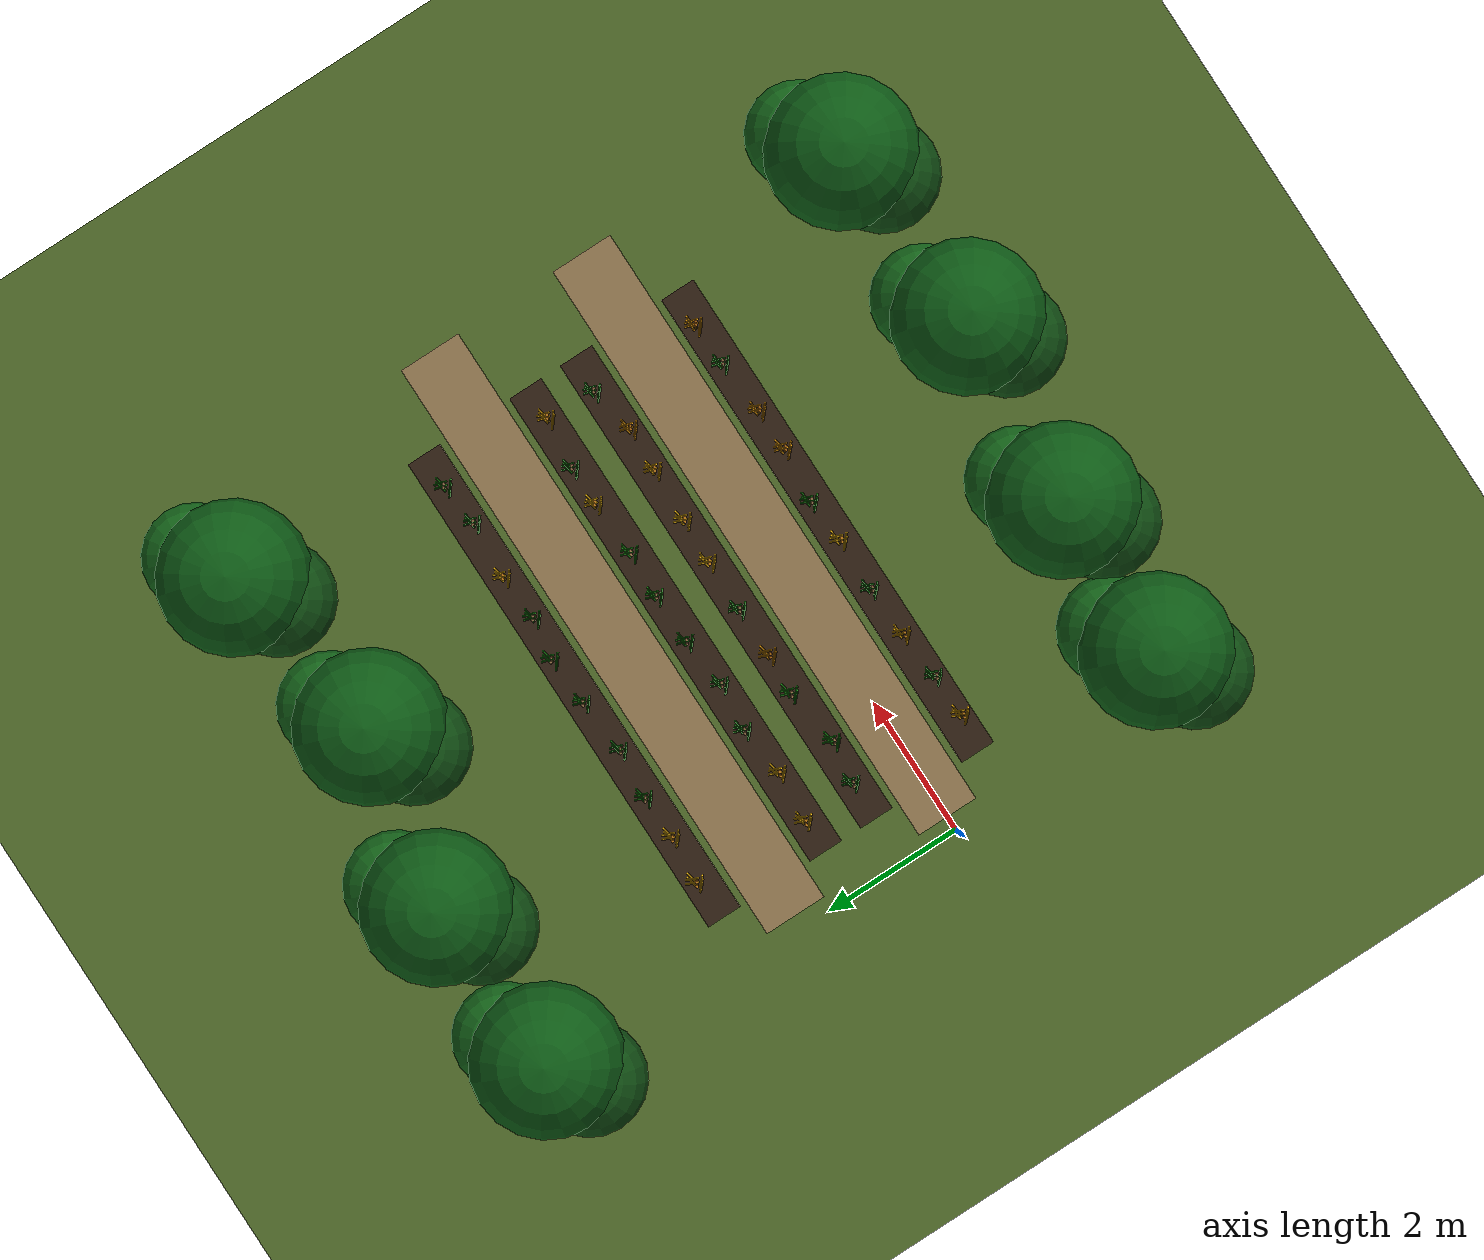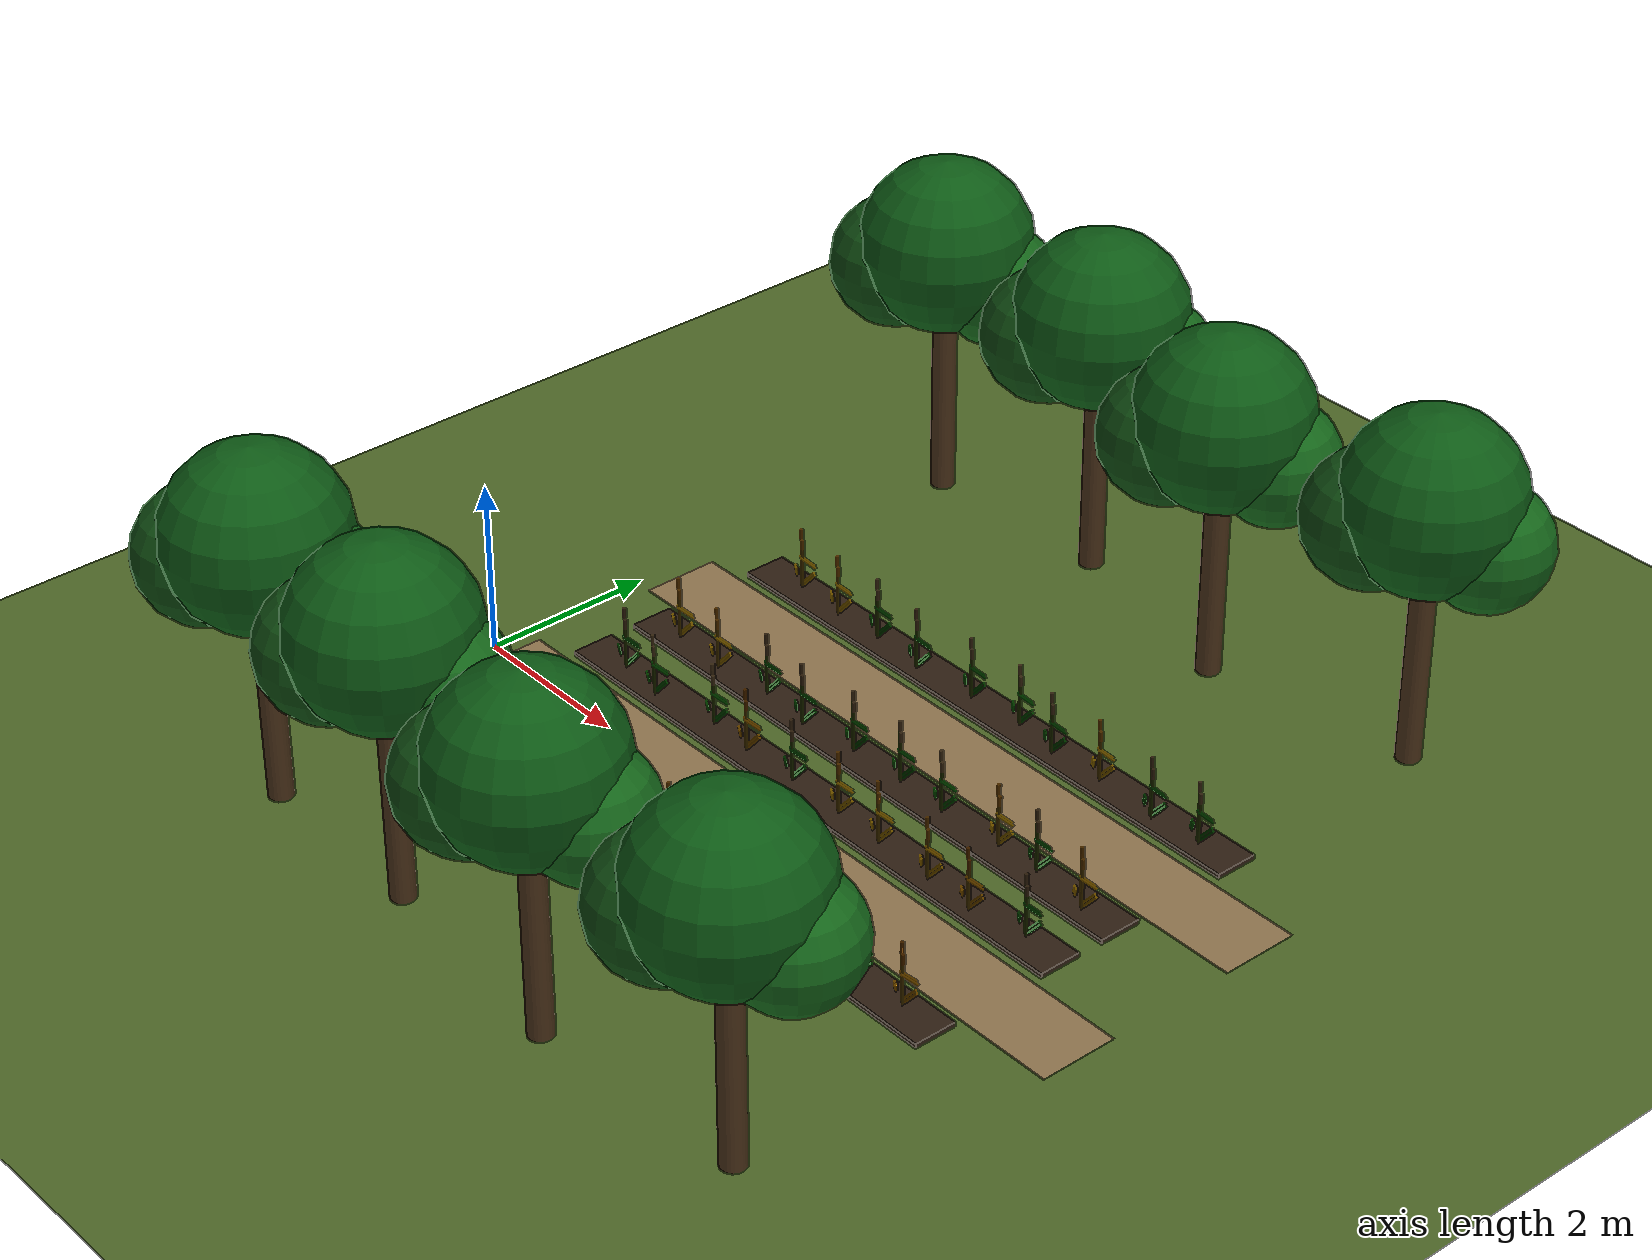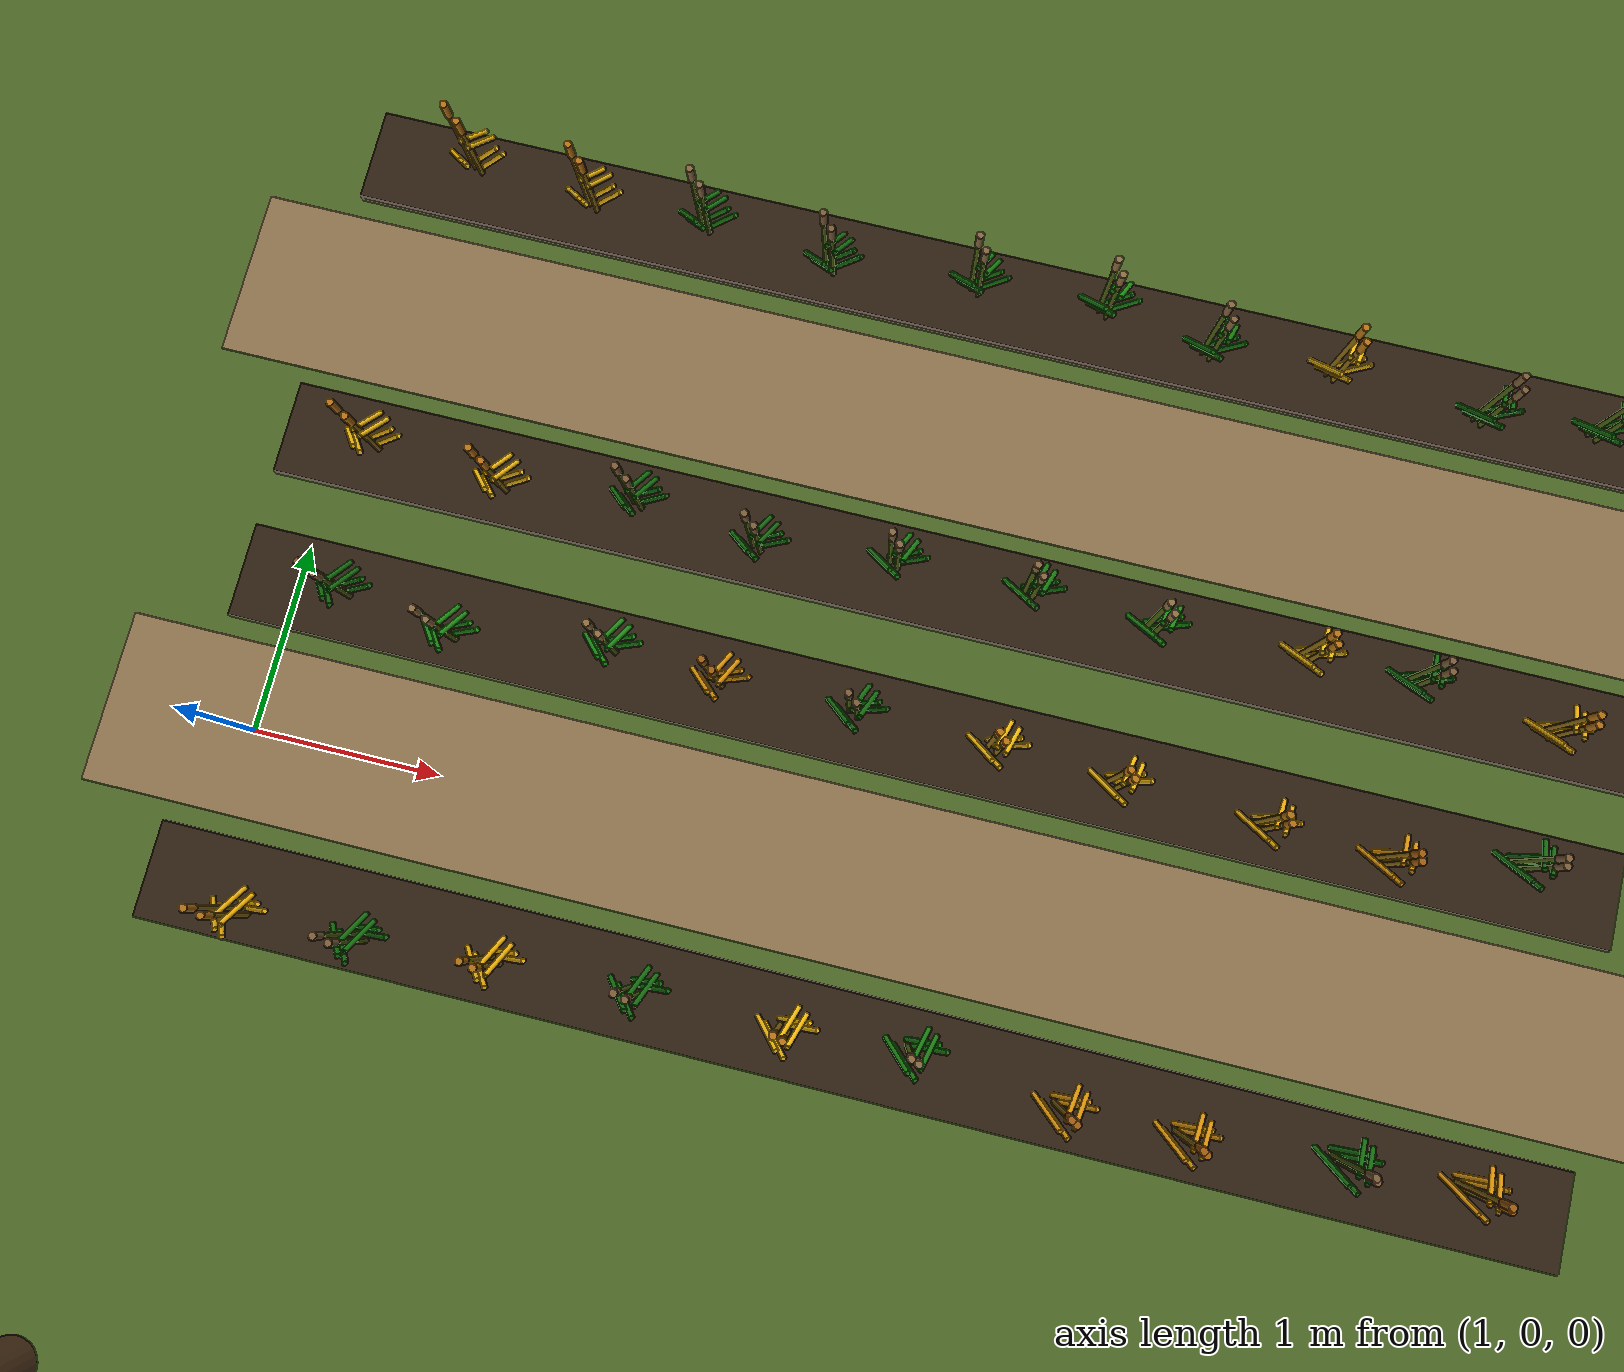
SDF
<?xml version="1.0"?>
<sdf version="1.6">
  <world name="default">
    <plugin filename="gz-sim-physics-system" name="gz::sim::systems::Physics"/>
    <plugin filename="gz-sim-user-commands-system" name="gz::sim::systems::UserCommands"/>
    <plugin filename="gz-sim-scene-broadcaster-system" name="gz::sim::systems::SceneBroadcaster"/>
    <plugin filename="gz-sim-sensors-system" name="gz::sim::systems::Sensors">
      <render_engine>ogre2</render_engine>
    </plugin>
    <plugin filename="gz-sim-imu-system" name="gz::sim::systems::Imu"/>

    <scene>
      <ambient>0.6 0.6 0.6 1</ambient>
      <background>0.5 0.7 0.9 1</background>
      <shadows>false</shadows>
    </scene>

    <physics type="ode">
      <real_time_update_rate>1000.0</real_time_update_rate>
      <max_step_size>0.001</max_step_size>
      <real_time_factor>1</real_time_factor>
    </physics>

    <light type="directional" name="sun">
      <cast_shadows>false</cast_shadows>
      <pose>0 0 10 0 0 0</pose>
      <diffuse>0.9 0.9 0.9 1</diffuse>
      <specular>0.2 0.2 0.2 1</specular>
      <direction>-0.5 0.1 -0.9</direction>
    </light>

    <model name="ground">
      <static>true</static>
      <link name="link">
        <collision name="col">
          <geometry><plane><normal>0 0 1</normal><size>40 40</size></plane></geometry>
        </collision>
        <visual name="vis">
          <geometry><plane><normal>0 0 1</normal><size>40 40</size></plane></geometry>
          <material><ambient>0.30 0.40 0.15 1</ambient><diffuse>0.30 0.40 0.15 1</diffuse></material>
        </visual>
      </link>
    </model>
    <model name="path_1">
      <static>true</static>
      <pose>4.65 0.00 0.002 0 0 0.00</pose>
      <link name="link">
        <visual name="v">
          <geometry><box><size>8.90 0.90 0.004</size></box></geometry>
          <material><ambient>0.55 0.45 0.30 1</ambient><diffuse>0.55 0.45 0.30 1</diffuse></material>
        </visual>
      </link>
    </model>
    <model name="bed_1a">
      <static>true</static>
      <pose>4.35 -0.80 0.030 0 0 0.00</pose>
      <link name="link">
        <visual name="v">
          <geometry><box><size>7.30 0.50 0.060</size></box></geometry>
          <material><ambient>0.18 0.12 0.07 1</ambient><diffuse>0.18 0.12 0.07 1</diffuse></material>
        </visual>
      </link>
    </model>
    <model name="plant_01">
      <static>true</static>
      <pose>1.22 -0.88 0 0 0 0</pose>
      <link name="link">
        <visual name="stem_0">
          <pose>0.000 0.000 0.320 0.000 0.000 0.000</pose>
          <geometry><cylinder><radius>0.014</radius><length>0.64</length></cylinder></geometry>
          <material><ambient>0.55 0.42 0.08 1</ambient><diffuse>0.55 0.42 0.08 1</diffuse></material>
        </visual>
        <visual name="leaf_0_0">
          <pose>0.050 0.040 0.130 0.000 0.700 0.150</pose>
          <geometry><cylinder><radius>0.014</radius><length>0.3</length></cylinder></geometry>
          <material><ambient>0.92 0.68 0.04 1</ambient><diffuse>0.92 0.68 0.04 1</diffuse></material>
        </visual>
        <visual name="leaf_0_1">
          <pose>-0.050 -0.040 0.250 0.000 -0.720 2.400</pose>
          <geometry><cylinder><radius>0.014</radius><length>0.28</length></cylinder></geometry>
          <material><ambient>0.92 0.68 0.04 1</ambient><diffuse>0.92 0.68 0.04 1</diffuse></material>
        </visual>
        <visual name="leaf_0_2">
          <pose>0.050 0.040 0.360 0.000 0.780 4.400</pose>
          <geometry><cylinder><radius>0.014</radius><length>0.24</length></cylinder></geometry>
          <material><ambient>0.92 0.68 0.04 1</ambient><diffuse>0.92 0.68 0.04 1</diffuse></material>
        </visual>
        <visual name="ear_0">
          <pose>0.000 0.000 0.700 0.000 0.000 0.000</pose>
          <geometry><cylinder><radius>0.02</radius><length>0.12</length></cylinder></geometry>
          <material><ambient>0.68 0.43 0.08 1</ambient><diffuse>0.68 0.43 0.08 1</diffuse></material>
        </visual>
        <visual name="stem_1">
          <pose>0.045 -0.025 0.265 0.000 0.000 0.000</pose>
          <geometry><cylinder><radius>0.014</radius><length>0.53</length></cylinder></geometry>
          <material><ambient>0.55 0.42 0.08 1</ambient><diffuse>0.55 0.42 0.08 1</diffuse></material>
        </visual>
        <visual name="leaf_1_0">
          <pose>0.095 0.015 0.130 0.000 0.700 0.150</pose>
          <geometry><cylinder><radius>0.014</radius><length>0.3</length></cylinder></geometry>
          <material><ambient>0.92 0.68 0.04 1</ambient><diffuse>0.92 0.68 0.04 1</diffuse></material>
        </visual>
        <visual name="leaf_1_1">
          <pose>-0.005 -0.065 0.250 0.000 -0.720 2.400</pose>
          <geometry><cylinder><radius>0.014</radius><length>0.28</length></cylinder></geometry>
          <material><ambient>0.92 0.68 0.04 1</ambient><diffuse>0.92 0.68 0.04 1</diffuse></material>
        </visual>
        <visual name="leaf_1_2">
          <pose>0.095 0.015 0.360 0.000 0.780 4.400</pose>
          <geometry><cylinder><radius>0.014</radius><length>0.24</length></cylinder></geometry>
          <material><ambient>0.92 0.68 0.04 1</ambient><diffuse>0.92 0.68 0.04 1</diffuse></material>
        </visual>
        <visual name="ear_1">
          <pose>0.045 -0.025 0.590 0.000 0.000 0.000</pose>
          <geometry><cylinder><radius>0.02</radius><length>0.12</length></cylinder></geometry>
          <material><ambient>0.68 0.43 0.08 1</ambient><diffuse>0.68 0.43 0.08 1</diffuse></material>
        </visual>
      </link>
    </model>
    <model name="plant_02">
      <static>true</static>
      <pose>1.84 -0.86 0 0 0 0</pose>
      <link name="link">
        <visual name="stem_0">
          <pose>0.000 0.000 0.320 0.000 0.000 0.000</pose>
          <geometry><cylinder><radius>0.014</radius><length>0.64</length></cylinder></geometry>
          <material><ambient>0.30 0.38 0.08 1</ambient><diffuse>0.30 0.38 0.08 1</diffuse></material>
        </visual>
        <visual name="leaf_0_0">
          <pose>0.050 0.040 0.130 0.000 0.700 0.150</pose>
          <geometry><cylinder><radius>0.014</radius><length>0.3</length></cylinder></geometry>
          <material><ambient>0.08 0.42 0.05 1</ambient><diffuse>0.08 0.42 0.05 1</diffuse></material>
        </visual>
        <visual name="leaf_0_1">
          <pose>-0.050 -0.040 0.250 0.000 -0.720 2.400</pose>
          <geometry><cylinder><radius>0.014</radius><length>0.28</length></cylinder></geometry>
          <material><ambient>0.08 0.42 0.05 1</ambient><diffuse>0.08 0.42 0.05 1</diffuse></material>
        </visual>
        <visual name="leaf_0_2">
          <pose>0.050 0.040 0.360 0.000 0.780 4.400</pose>
          <geometry><cylinder><radius>0.014</radius><length>0.24</length></cylinder></geometry>
          <material><ambient>0.08 0.42 0.05 1</ambient><diffuse>0.08 0.42 0.05 1</diffuse></material>
        </visual>
        <visual name="ear_0">
          <pose>0.000 0.000 0.700 0.000 0.000 0.000</pose>
          <geometry><cylinder><radius>0.02</radius><length>0.12</length></cylinder></geometry>
          <material><ambient>0.48 0.36 0.22 1</ambient><diffuse>0.48 0.36 0.22 1</diffuse></material>
        </visual>
        <visual name="stem_1">
          <pose>0.045 -0.025 0.265 0.000 0.000 0.000</pose>
          <geometry><cylinder><radius>0.014</radius><length>0.53</length></cylinder></geometry>
          <material><ambient>0.30 0.38 0.08 1</ambient><diffuse>0.30 0.38 0.08 1</diffuse></material>
        </visual>
        <visual name="leaf_1_0">
          <pose>0.095 0.015 0.130 0.000 0.700 0.150</pose>
          <geometry><cylinder><radius>0.014</radius><length>0.3</length></cylinder></geometry>
          <material><ambient>0.08 0.42 0.05 1</ambient><diffuse>0.08 0.42 0.05 1</diffuse></material>
        </visual>
        <visual name="leaf_1_1">
          <pose>-0.005 -0.065 0.250 0.000 -0.720 2.400</pose>
          <geometry><cylinder><radius>0.014</radius><length>0.28</length></cylinder></geometry>
          <material><ambient>0.08 0.42 0.05 1</ambient><diffuse>0.08 0.42 0.05 1</diffuse></material>
        </visual>
        <visual name="leaf_1_2">
          <pose>0.095 0.015 0.360 0.000 0.780 4.400</pose>
          <geometry><cylinder><radius>0.014</radius><length>0.24</length></cylinder></geometry>
          <material><ambient>0.08 0.42 0.05 1</ambient><diffuse>0.08 0.42 0.05 1</diffuse></material>
        </visual>
        <visual name="ear_1">
          <pose>0.045 -0.025 0.590 0.000 0.000 0.000</pose>
          <geometry><cylinder><radius>0.02</radius><length>0.12</length></cylinder></geometry>
          <material><ambient>0.48 0.36 0.22 1</ambient><diffuse>0.48 0.36 0.22 1</diffuse></material>
        </visual>
      </link>
    </model>
    <model name="plant_03">
      <static>true</static>
      <pose>2.53 -0.81 0 0 0 0</pose>
      <link name="link">
        <visual name="stem_0">
          <pose>0.000 0.000 0.320 0.000 0.000 0.000</pose>
          <geometry><cylinder><radius>0.014</radius><length>0.64</length></cylinder></geometry>
          <material><ambient>0.55 0.42 0.08 1</ambient><diffuse>0.55 0.42 0.08 1</diffuse></material>
        </visual>
        <visual name="leaf_0_0">
          <pose>0.050 0.040 0.130 0.000 0.700 0.150</pose>
          <geometry><cylinder><radius>0.014</radius><length>0.3</length></cylinder></geometry>
          <material><ambient>0.92 0.68 0.04 1</ambient><diffuse>0.92 0.68 0.04 1</diffuse></material>
        </visual>
        <visual name="leaf_0_1">
          <pose>-0.050 -0.040 0.250 0.000 -0.720 2.400</pose>
          <geometry><cylinder><radius>0.014</radius><length>0.28</length></cylinder></geometry>
          <material><ambient>0.92 0.68 0.04 1</ambient><diffuse>0.92 0.68 0.04 1</diffuse></material>
        </visual>
        <visual name="leaf_0_2">
          <pose>0.050 0.040 0.360 0.000 0.780 4.400</pose>
          <geometry><cylinder><radius>0.014</radius><length>0.24</length></cylinder></geometry>
          <material><ambient>0.92 0.68 0.04 1</ambient><diffuse>0.92 0.68 0.04 1</diffuse></material>
        </visual>
        <visual name="ear_0">
          <pose>0.000 0.000 0.700 0.000 0.000 0.000</pose>
          <geometry><cylinder><radius>0.02</radius><length>0.12</length></cylinder></geometry>
          <material><ambient>0.68 0.43 0.08 1</ambient><diffuse>0.68 0.43 0.08 1</diffuse></material>
        </visual>
        <visual name="stem_1">
          <pose>0.045 -0.025 0.265 0.000 0.000 0.000</pose>
          <geometry><cylinder><radius>0.014</radius><length>0.53</length></cylinder></geometry>
          <material><ambient>0.55 0.42 0.08 1</ambient><diffuse>0.55 0.42 0.08 1</diffuse></material>
        </visual>
        <visual name="leaf_1_0">
          <pose>0.095 0.015 0.130 0.000 0.700 0.150</pose>
          <geometry><cylinder><radius>0.014</radius><length>0.3</length></cylinder></geometry>
          <material><ambient>0.92 0.68 0.04 1</ambient><diffuse>0.92 0.68 0.04 1</diffuse></material>
        </visual>
        <visual name="leaf_1_1">
          <pose>-0.005 -0.065 0.250 0.000 -0.720 2.400</pose>
          <geometry><cylinder><radius>0.014</radius><length>0.28</length></cylinder></geometry>
          <material><ambient>0.92 0.68 0.04 1</ambient><diffuse>0.92 0.68 0.04 1</diffuse></material>
        </visual>
        <visual name="leaf_1_2">
          <pose>0.095 0.015 0.360 0.000 0.780 4.400</pose>
          <geometry><cylinder><radius>0.014</radius><length>0.24</length></cylinder></geometry>
          <material><ambient>0.92 0.68 0.04 1</ambient><diffuse>0.92 0.68 0.04 1</diffuse></material>
        </visual>
        <visual name="ear_1">
          <pose>0.045 -0.025 0.590 0.000 0.000 0.000</pose>
          <geometry><cylinder><radius>0.02</radius><length>0.12</length></cylinder></geometry>
          <material><ambient>0.68 0.43 0.08 1</ambient><diffuse>0.68 0.43 0.08 1</diffuse></material>
        </visual>
      </link>
    </model>
    <model name="plant_04">
      <static>true</static>
      <pose>3.26 -0.78 0 0 0 0</pose>
      <link name="link">
        <visual name="stem_0">
          <pose>0.000 0.000 0.320 0.000 0.000 0.000</pose>
          <geometry><cylinder><radius>0.014</radius><length>0.64</length></cylinder></geometry>
          <material><ambient>0.30 0.38 0.08 1</ambient><diffuse>0.30 0.38 0.08 1</diffuse></material>
        </visual>
        <visual name="leaf_0_0">
          <pose>0.050 0.040 0.130 0.000 0.700 0.150</pose>
          <geometry><cylinder><radius>0.014</radius><length>0.3</length></cylinder></geometry>
          <material><ambient>0.08 0.42 0.05 1</ambient><diffuse>0.08 0.42 0.05 1</diffuse></material>
        </visual>
        <visual name="leaf_0_1">
          <pose>-0.050 -0.040 0.250 0.000 -0.720 2.400</pose>
          <geometry><cylinder><radius>0.014</radius><length>0.28</length></cylinder></geometry>
          <material><ambient>0.08 0.42 0.05 1</ambient><diffuse>0.08 0.42 0.05 1</diffuse></material>
        </visual>
        <visual name="leaf_0_2">
          <pose>0.050 0.040 0.360 0.000 0.780 4.400</pose>
          <geometry><cylinder><radius>0.014</radius><length>0.24</length></cylinder></geometry>
          <material><ambient>0.08 0.42 0.05 1</ambient><diffuse>0.08 0.42 0.05 1</diffuse></material>
        </visual>
        <visual name="ear_0">
          <pose>0.000 0.000 0.700 0.000 0.000 0.000</pose>
          <geometry><cylinder><radius>0.02</radius><length>0.12</length></cylinder></geometry>
          <material><ambient>0.48 0.36 0.22 1</ambient><diffuse>0.48 0.36 0.22 1</diffuse></material>
        </visual>
        <visual name="stem_1">
          <pose>0.045 -0.025 0.265 0.000 0.000 0.000</pose>
          <geometry><cylinder><radius>0.014</radius><length>0.53</length></cylinder></geometry>
          <material><ambient>0.30 0.38 0.08 1</ambient><diffuse>0.30 0.38 0.08 1</diffuse></material>
        </visual>
        <visual name="leaf_1_0">
          <pose>0.095 0.015 0.130 0.000 0.700 0.150</pose>
          <geometry><cylinder><radius>0.014</radius><length>0.3</length></cylinder></geometry>
          <material><ambient>0.08 0.42 0.05 1</ambient><diffuse>0.08 0.42 0.05 1</diffuse></material>
        </visual>
        <visual name="leaf_1_1">
          <pose>-0.005 -0.065 0.250 0.000 -0.720 2.400</pose>
          <geometry><cylinder><radius>0.014</radius><length>0.28</length></cylinder></geometry>
          <material><ambient>0.08 0.42 0.05 1</ambient><diffuse>0.08 0.42 0.05 1</diffuse></material>
        </visual>
        <visual name="leaf_1_2">
          <pose>0.095 0.015 0.360 0.000 0.780 4.400</pose>
          <geometry><cylinder><radius>0.014</radius><length>0.24</length></cylinder></geometry>
          <material><ambient>0.08 0.42 0.05 1</ambient><diffuse>0.08 0.42 0.05 1</diffuse></material>
        </visual>
        <visual name="ear_1">
          <pose>0.045 -0.025 0.590 0.000 0.000 0.000</pose>
          <geometry><cylinder><radius>0.02</radius><length>0.12</length></cylinder></geometry>
          <material><ambient>0.48 0.36 0.22 1</ambient><diffuse>0.48 0.36 0.22 1</diffuse></material>
        </visual>
      </link>
    </model>
    <model name="plant_05">
      <static>true</static>
      <pose>4.02 -0.79 0 0 0 0</pose>
      <link name="link">
        <visual name="stem_0">
          <pose>0.000 0.000 0.320 0.000 0.000 0.000</pose>
          <geometry><cylinder><radius>0.014</radius><length>0.64</length></cylinder></geometry>
          <material><ambient>0.55 0.42 0.08 1</ambient><diffuse>0.55 0.42 0.08 1</diffuse></material>
        </visual>
        <visual name="leaf_0_0">
          <pose>0.050 0.040 0.130 0.000 0.700 0.150</pose>
          <geometry><cylinder><radius>0.014</radius><length>0.3</length></cylinder></geometry>
          <material><ambient>0.95 0.73 0.06 1</ambient><diffuse>0.95 0.73 0.06 1</diffuse></material>
        </visual>
        <visual name="leaf_0_1">
          <pose>-0.050 -0.040 0.250 0.000 -0.720 2.400</pose>
          <geometry><cylinder><radius>0.014</radius><length>0.28</length></cylinder></geometry>
          <material><ambient>0.95 0.73 0.06 1</ambient><diffuse>0.95 0.73 0.06 1</diffuse></material>
        </visual>
        <visual name="leaf_0_2">
          <pose>0.050 0.040 0.360 0.000 0.780 4.400</pose>
          <geometry><cylinder><radius>0.014</radius><length>0.24</length></cylinder></geometry>
          <material><ambient>0.95 0.73 0.06 1</ambient><diffuse>0.95 0.73 0.06 1</diffuse></material>
        </visual>
        <visual name="ear_0">
          <pose>0.000 0.000 0.700 0.000 0.000 0.000</pose>
          <geometry><cylinder><radius>0.02</radius><length>0.12</length></cylinder></geometry>
          <material><ambient>0.72 0.45 0.08 1</ambient><diffuse>0.72 0.45 0.08 1</diffuse></material>
        </visual>
        <visual name="stem_1">
          <pose>0.045 -0.025 0.265 0.000 0.000 0.000</pose>
          <geometry><cylinder><radius>0.014</radius><length>0.53</length></cylinder></geometry>
          <material><ambient>0.55 0.42 0.08 1</ambient><diffuse>0.55 0.42 0.08 1</diffuse></material>
        </visual>
        <visual name="leaf_1_0">
          <pose>0.095 0.015 0.130 0.000 0.700 0.150</pose>
          <geometry><cylinder><radius>0.014</radius><length>0.3</length></cylinder></geometry>
          <material><ambient>0.95 0.73 0.06 1</ambient><diffuse>0.95 0.73 0.06 1</diffuse></material>
        </visual>
        <visual name="leaf_1_1">
          <pose>-0.005 -0.065 0.250 0.000 -0.720 2.400</pose>
          <geometry><cylinder><radius>0.014</radius><length>0.28</length></cylinder></geometry>
          <material><ambient>0.95 0.73 0.06 1</ambient><diffuse>0.95 0.73 0.06 1</diffuse></material>
        </visual>
        <visual name="leaf_1_2">
          <pose>0.095 0.015 0.360 0.000 0.780 4.400</pose>
          <geometry><cylinder><radius>0.014</radius><length>0.24</length></cylinder></geometry>
          <material><ambient>0.95 0.73 0.06 1</ambient><diffuse>0.95 0.73 0.06 1</diffuse></material>
        </visual>
        <visual name="ear_1">
          <pose>0.045 -0.025 0.590 0.000 0.000 0.000</pose>
          <geometry><cylinder><radius>0.02</radius><length>0.12</length></cylinder></geometry>
          <material><ambient>0.72 0.45 0.08 1</ambient><diffuse>0.72 0.45 0.08 1</diffuse></material>
        </visual>
      </link>
    </model>
    <model name="plant_06">
      <static>true</static>
      <pose>4.66 -0.74 0 0 0 0</pose>
      <link name="link">
        <visual name="stem_0">
          <pose>0.000 0.000 0.320 0.000 0.000 0.000</pose>
          <geometry><cylinder><radius>0.014</radius><length>0.64</length></cylinder></geometry>
          <material><ambient>0.30 0.38 0.08 1</ambient><diffuse>0.30 0.38 0.08 1</diffuse></material>
        </visual>
        <visual name="leaf_0_0">
          <pose>0.050 0.040 0.130 0.000 0.700 0.150</pose>
          <geometry><cylinder><radius>0.014</radius><length>0.3</length></cylinder></geometry>
          <material><ambient>0.10 0.48 0.06 1</ambient><diffuse>0.10 0.48 0.06 1</diffuse></material>
        </visual>
        <visual name="leaf_0_1">
          <pose>-0.050 -0.040 0.250 0.000 -0.720 2.400</pose>
          <geometry><cylinder><radius>0.014</radius><length>0.28</length></cylinder></geometry>
          <material><ambient>0.10 0.48 0.06 1</ambient><diffuse>0.10 0.48 0.06 1</diffuse></material>
        </visual>
        <visual name="leaf_0_2">
          <pose>0.050 0.040 0.360 0.000 0.780 4.400</pose>
          <geometry><cylinder><radius>0.014</radius><length>0.24</length></cylinder></geometry>
          <material><ambient>0.10 0.48 0.06 1</ambient><diffuse>0.10 0.48 0.06 1</diffuse></material>
        </visual>
        <visual name="ear_0">
          <pose>0.000 0.000 0.700 0.000 0.000 0.000</pose>
          <geometry><cylinder><radius>0.02</radius><length>0.12</length></cylinder></geometry>
          <material><ambient>0.52 0.40 0.25 1</ambient><diffuse>0.52 0.40 0.25 1</diffuse></material>
        </visual>
        <visual name="stem_1">
          <pose>0.045 -0.025 0.265 0.000 0.000 0.000</pose>
          <geometry><cylinder><radius>0.014</radius><length>0.53</length></cylinder></geometry>
          <material><ambient>0.30 0.38 0.08 1</ambient><diffuse>0.30 0.38 0.08 1</diffuse></material>
        </visual>
        <visual name="leaf_1_0">
          <pose>0.095 0.015 0.130 0.000 0.700 0.150</pose>
          <geometry><cylinder><radius>0.014</radius><length>0.3</length></cylinder></geometry>
          <material><ambient>0.10 0.48 0.06 1</ambient><diffuse>0.10 0.48 0.06 1</diffuse></material>
        </visual>
        <visual name="leaf_1_1">
          <pose>-0.005 -0.065 0.250 0.000 -0.720 2.400</pose>
          <geometry><cylinder><radius>0.014</radius><length>0.28</length></cylinder></geometry>
          <material><ambient>0.10 0.48 0.06 1</ambient><diffuse>0.10 0.48 0.06 1</diffuse></material>
        </visual>
        <visual name="leaf_1_2">
          <pose>0.095 0.015 0.360 0.000 0.780 4.400</pose>
          <geometry><cylinder><radius>0.014</radius><length>0.24</length></cylinder></geometry>
          <material><ambient>0.10 0.48 0.06 1</ambient><diffuse>0.10 0.48 0.06 1</diffuse></material>
        </visual>
        <visual name="ear_1">
          <pose>0.045 -0.025 0.590 0.000 0.000 0.000</pose>
          <geometry><cylinder><radius>0.02</radius><length>0.12</length></cylinder></geometry>
          <material><ambient>0.52 0.40 0.25 1</ambient><diffuse>0.52 0.40 0.25 1</diffuse></material>
        </visual>
      </link>
    </model>
    <model name="plant_07">
      <static>true</static>
      <pose>5.43 -0.83 0 0 0 0</pose>
      <link name="link">
        <visual name="stem_0">
          <pose>0.000 0.000 0.320 0.000 0.000 0.000</pose>
          <geometry><cylinder><radius>0.014</radius><length>0.64</length></cylinder></geometry>
          <material><ambient>0.55 0.42 0.08 1</ambient><diffuse>0.55 0.42 0.08 1</diffuse></material>
        </visual>
        <visual name="leaf_0_0">
          <pose>0.050 0.040 0.130 0.000 0.700 0.150</pose>
          <geometry><cylinder><radius>0.014</radius><length>0.3</length></cylinder></geometry>
          <material><ambient>0.86 0.58 0.04 1</ambient><diffuse>0.86 0.58 0.04 1</diffuse></material>
        </visual>
        <visual name="leaf_0_1">
          <pose>-0.050 -0.040 0.250 0.000 -0.720 2.400</pose>
          <geometry><cylinder><radius>0.014</radius><length>0.28</length></cylinder></geometry>
          <material><ambient>0.86 0.58 0.04 1</ambient><diffuse>0.86 0.58 0.04 1</diffuse></material>
        </visual>
        <visual name="leaf_0_2">
          <pose>0.050 0.040 0.360 0.000 0.780 4.400</pose>
          <geometry><cylinder><radius>0.014</radius><length>0.24</length></cylinder></geometry>
          <material><ambient>0.86 0.58 0.04 1</ambient><diffuse>0.86 0.58 0.04 1</diffuse></material>
        </visual>
        <visual name="ear_0">
          <pose>0.000 0.000 0.700 0.000 0.000 0.000</pose>
          <geometry><cylinder><radius>0.02</radius><length>0.12</length></cylinder></geometry>
          <material><ambient>0.62 0.36 0.06 1</ambient><diffuse>0.62 0.36 0.06 1</diffuse></material>
        </visual>
        <visual name="stem_1">
          <pose>0.045 -0.025 0.265 0.000 0.000 0.000</pose>
          <geometry><cylinder><radius>0.014</radius><length>0.53</length></cylinder></geometry>
          <material><ambient>0.55 0.42 0.08 1</ambient><diffuse>0.55 0.42 0.08 1</diffuse></material>
        </visual>
        <visual name="leaf_1_0">
          <pose>0.095 0.015 0.130 0.000 0.700 0.150</pose>
          <geometry><cylinder><radius>0.014</radius><length>0.3</length></cylinder></geometry>
          <material><ambient>0.86 0.58 0.04 1</ambient><diffuse>0.86 0.58 0.04 1</diffuse></material>
        </visual>
        <visual name="leaf_1_1">
          <pose>-0.005 -0.065 0.250 0.000 -0.720 2.400</pose>
          <geometry><cylinder><radius>0.014</radius><length>0.28</length></cylinder></geometry>
          <material><ambient>0.86 0.58 0.04 1</ambient><diffuse>0.86 0.58 0.04 1</diffuse></material>
        </visual>
        <visual name="leaf_1_2">
          <pose>0.095 0.015 0.360 0.000 0.780 4.400</pose>
          <geometry><cylinder><radius>0.014</radius><length>0.24</length></cylinder></geometry>
          <material><ambient>0.86 0.58 0.04 1</ambient><diffuse>0.86 0.58 0.04 1</diffuse></material>
        </visual>
        <visual name="ear_1">
          <pose>0.045 -0.025 0.590 0.000 0.000 0.000</pose>
          <geometry><cylinder><radius>0.02</radius><length>0.12</length></cylinder></geometry>
          <material><ambient>0.62 0.36 0.06 1</ambient><diffuse>0.62 0.36 0.06 1</diffuse></material>
        </visual>
      </link>
    </model>
    <model name="plant_08">
      <static>true</static>
      <pose>6.04 -0.82 0 0 0 0</pose>
      <link name="link">
        <visual name="stem_0">
          <pose>0.000 0.000 0.320 0.000 0.000 0.000</pose>
          <geometry><cylinder><radius>0.014</radius><length>0.64</length></cylinder></geometry>
          <material><ambient>0.55 0.42 0.08 1</ambient><diffuse>0.55 0.42 0.08 1</diffuse></material>
        </visual>
        <visual name="leaf_0_0">
          <pose>0.050 0.040 0.130 0.000 0.700 0.150</pose>
          <geometry><cylinder><radius>0.014</radius><length>0.3</length></cylinder></geometry>
          <material><ambient>0.86 0.58 0.04 1</ambient><diffuse>0.86 0.58 0.04 1</diffuse></material>
        </visual>
        <visual name="leaf_0_1">
          <pose>-0.050 -0.040 0.250 0.000 -0.720 2.400</pose>
          <geometry><cylinder><radius>0.014</radius><length>0.28</length></cylinder></geometry>
          <material><ambient>0.86 0.58 0.04 1</ambient><diffuse>0.86 0.58 0.04 1</diffuse></material>
        </visual>
        <visual name="leaf_0_2">
          <pose>0.050 0.040 0.360 0.000 0.780 4.400</pose>
          <geometry><cylinder><radius>0.014</radius><length>0.24</length></cylinder></geometry>
          <material><ambient>0.86 0.58 0.04 1</ambient><diffuse>0.86 0.58 0.04 1</diffuse></material>
        </visual>
        <visual name="ear_0">
          <pose>0.000 0.000 0.700 0.000 0.000 0.000</pose>
          <geometry><cylinder><radius>0.02</radius><length>0.12</length></cylinder></geometry>
          <material><ambient>0.62 0.36 0.06 1</ambient><diffuse>0.62 0.36 0.06 1</diffuse></material>
        </visual>
        <visual name="stem_1">
          <pose>0.045 -0.025 0.265 0.000 0.000 0.000</pose>
          <geometry><cylinder><radius>0.014</radius><length>0.53</length></cylinder></geometry>
          <material><ambient>0.55 0.42 0.08 1</ambient><diffuse>0.55 0.42 0.08 1</diffuse></material>
        </visual>
        <visual name="leaf_1_0">
          <pose>0.095 0.015 0.130 0.000 0.700 0.150</pose>
          <geometry><cylinder><radius>0.014</radius><length>0.3</length></cylinder></geometry>
          <material><ambient>0.86 0.58 0.04 1</ambient><diffuse>0.86 0.58 0.04 1</diffuse></material>
        </visual>
        <visual name="leaf_1_1">
          <pose>-0.005 -0.065 0.250 0.000 -0.720 2.400</pose>
          <geometry><cylinder><radius>0.014</radius><length>0.28</length></cylinder></geometry>
          <material><ambient>0.86 0.58 0.04 1</ambient><diffuse>0.86 0.58 0.04 1</diffuse></material>
        </visual>
        <visual name="leaf_1_2">
          <pose>0.095 0.015 0.360 0.000 0.780 4.400</pose>
          <geometry><cylinder><radius>0.014</radius><length>0.24</length></cylinder></geometry>
          <material><ambient>0.86 0.58 0.04 1</ambient><diffuse>0.86 0.58 0.04 1</diffuse></material>
        </visual>
        <visual name="ear_1">
          <pose>0.045 -0.025 0.590 0.000 0.000 0.000</pose>
          <geometry><cylinder><radius>0.02</radius><length>0.12</length></cylinder></geometry>
          <material><ambient>0.62 0.36 0.06 1</ambient><diffuse>0.62 0.36 0.06 1</diffuse></material>
        </visual>
      </link>
    </model>
    <model name="plant_09">
      <static>true</static>
      <pose>6.82 -0.75 0 0 0 0</pose>
      <link name="link">
        <visual name="stem_0">
          <pose>0.000 0.000 0.320 0.000 0.000 0.000</pose>
          <geometry><cylinder><radius>0.014</radius><length>0.64</length></cylinder></geometry>
          <material><ambient>0.30 0.38 0.08 1</ambient><diffuse>0.30 0.38 0.08 1</diffuse></material>
        </visual>
        <visual name="leaf_0_0">
          <pose>0.050 0.040 0.130 0.000 0.700 0.150</pose>
          <geometry><cylinder><radius>0.014</radius><length>0.3</length></cylinder></geometry>
          <material><ambient>0.08 0.42 0.05 1</ambient><diffuse>0.08 0.42 0.05 1</diffuse></material>
        </visual>
        <visual name="leaf_0_1">
          <pose>-0.050 -0.040 0.250 0.000 -0.720 2.400</pose>
          <geometry><cylinder><radius>0.014</radius><length>0.28</length></cylinder></geometry>
          <material><ambient>0.08 0.42 0.05 1</ambient><diffuse>0.08 0.42 0.05 1</diffuse></material>
        </visual>
        <visual name="leaf_0_2">
          <pose>0.050 0.040 0.360 0.000 0.780 4.400</pose>
          <geometry><cylinder><radius>0.014</radius><length>0.24</length></cylinder></geometry>
          <material><ambient>0.08 0.42 0.05 1</ambient><diffuse>0.08 0.42 0.05 1</diffuse></material>
        </visual>
        <visual name="ear_0">
          <pose>0.000 0.000 0.700 0.000 0.000 0.000</pose>
          <geometry><cylinder><radius>0.02</radius><length>0.12</length></cylinder></geometry>
          <material><ambient>0.48 0.36 0.22 1</ambient><diffuse>0.48 0.36 0.22 1</diffuse></material>
        </visual>
        <visual name="stem_1">
          <pose>0.045 -0.025 0.265 0.000 0.000 0.000</pose>
          <geometry><cylinder><radius>0.014</radius><length>0.53</length></cylinder></geometry>
          <material><ambient>0.30 0.38 0.08 1</ambient><diffuse>0.30 0.38 0.08 1</diffuse></material>
        </visual>
        <visual name="leaf_1_0">
          <pose>0.095 0.015 0.130 0.000 0.700 0.150</pose>
          <geometry><cylinder><radius>0.014</radius><length>0.3</length></cylinder></geometry>
          <material><ambient>0.08 0.42 0.05 1</ambient><diffuse>0.08 0.42 0.05 1</diffuse></material>
        </visual>
        <visual name="leaf_1_1">
          <pose>-0.005 -0.065 0.250 0.000 -0.720 2.400</pose>
          <geometry><cylinder><radius>0.014</radius><length>0.28</length></cylinder></geometry>
          <material><ambient>0.08 0.42 0.05 1</ambient><diffuse>0.08 0.42 0.05 1</diffuse></material>
        </visual>
        <visual name="leaf_1_2">
          <pose>0.095 0.015 0.360 0.000 0.780 4.400</pose>
          <geometry><cylinder><radius>0.014</radius><length>0.24</length></cylinder></geometry>
          <material><ambient>0.08 0.42 0.05 1</ambient><diffuse>0.08 0.42 0.05 1</diffuse></material>
        </visual>
        <visual name="ear_1">
          <pose>0.045 -0.025 0.590 0.000 0.000 0.000</pose>
          <geometry><cylinder><radius>0.02</radius><length>0.12</length></cylinder></geometry>
          <material><ambient>0.48 0.36 0.22 1</ambient><diffuse>0.48 0.36 0.22 1</diffuse></material>
        </visual>
      </link>
    </model>
    <model name="plant_10">
      <static>true</static>
      <pose>7.44 -0.73 0 0 0 0</pose>
      <link name="link">
        <visual name="stem_0">
          <pose>0.000 0.000 0.320 0.000 0.000 0.000</pose>
          <geometry><cylinder><radius>0.014</radius><length>0.64</length></cylinder></geometry>
          <material><ambient>0.55 0.42 0.08 1</ambient><diffuse>0.55 0.42 0.08 1</diffuse></material>
        </visual>
        <visual name="leaf_0_0">
          <pose>0.050 0.040 0.130 0.000 0.700 0.150</pose>
          <geometry><cylinder><radius>0.014</radius><length>0.3</length></cylinder></geometry>
          <material><ambient>0.86 0.58 0.04 1</ambient><diffuse>0.86 0.58 0.04 1</diffuse></material>
        </visual>
        <visual name="leaf_0_1">
          <pose>-0.050 -0.040 0.250 0.000 -0.720 2.400</pose>
          <geometry><cylinder><radius>0.014</radius><length>0.28</length></cylinder></geometry>
          <material><ambient>0.86 0.58 0.04 1</ambient><diffuse>0.86 0.58 0.04 1</diffuse></material>
        </visual>
        <visual name="leaf_0_2">
          <pose>0.050 0.040 0.360 0.000 0.780 4.400</pose>
          <geometry><cylinder><radius>0.014</radius><length>0.24</length></cylinder></geometry>
          <material><ambient>0.86 0.58 0.04 1</ambient><diffuse>0.86 0.58 0.04 1</diffuse></material>
        </visual>
        <visual name="ear_0">
          <pose>0.000 0.000 0.700 0.000 0.000 0.000</pose>
          <geometry><cylinder><radius>0.02</radius><length>0.12</length></cylinder></geometry>
          <material><ambient>0.62 0.36 0.06 1</ambient><diffuse>0.62 0.36 0.06 1</diffuse></material>
        </visual>
        <visual name="stem_1">
          <pose>0.045 -0.025 0.265 0.000 0.000 0.000</pose>
          <geometry><cylinder><radius>0.014</radius><length>0.53</length></cylinder></geometry>
          <material><ambient>0.55 0.42 0.08 1</ambient><diffuse>0.55 0.42 0.08 1</diffuse></material>
        </visual>
        <visual name="leaf_1_0">
          <pose>0.095 0.015 0.130 0.000 0.700 0.150</pose>
          <geometry><cylinder><radius>0.014</radius><length>0.3</length></cylinder></geometry>
          <material><ambient>0.86 0.58 0.04 1</ambient><diffuse>0.86 0.58 0.04 1</diffuse></material>
        </visual>
        <visual name="leaf_1_1">
          <pose>-0.005 -0.065 0.250 0.000 -0.720 2.400</pose>
          <geometry><cylinder><radius>0.014</radius><length>0.28</length></cylinder></geometry>
          <material><ambient>0.86 0.58 0.04 1</ambient><diffuse>0.86 0.58 0.04 1</diffuse></material>
        </visual>
        <visual name="leaf_1_2">
          <pose>0.095 0.015 0.360 0.000 0.780 4.400</pose>
          <geometry><cylinder><radius>0.014</radius><length>0.24</length></cylinder></geometry>
          <material><ambient>0.86 0.58 0.04 1</ambient><diffuse>0.86 0.58 0.04 1</diffuse></material>
        </visual>
        <visual name="ear_1">
          <pose>0.045 -0.025 0.590 0.000 0.000 0.000</pose>
          <geometry><cylinder><radius>0.02</radius><length>0.12</length></cylinder></geometry>
          <material><ambient>0.62 0.36 0.06 1</ambient><diffuse>0.62 0.36 0.06 1</diffuse></material>
        </visual>
      </link>
    </model>
    <model name="bed_1b">
      <static>true</static>
      <pose>4.35 0.80 0.030 0 0 0.00</pose>
      <link name="link">
        <visual name="v">
          <geometry><box><size>7.30 0.50 0.060</size></box></geometry>
          <material><ambient>0.18 0.12 0.07 1</ambient><diffuse>0.18 0.12 0.07 1</diffuse></material>
        </visual>
      </link>
    </model>
    <model name="plant_11">
      <static>true</static>
      <pose>1.25 0.82 0 0 0 0</pose>
      <link name="link">
        <visual name="stem_0">
          <pose>0.000 0.000 0.320 0.000 0.000 0.000</pose>
          <geometry><cylinder><radius>0.014</radius><length>0.64</length></cylinder></geometry>
          <material><ambient>0.30 0.38 0.08 1</ambient><diffuse>0.30 0.38 0.08 1</diffuse></material>
        </visual>
        <visual name="leaf_0_0">
          <pose>0.050 0.040 0.130 0.000 0.700 0.150</pose>
          <geometry><cylinder><radius>0.014</radius><length>0.3</length></cylinder></geometry>
          <material><ambient>0.08 0.42 0.05 1</ambient><diffuse>0.08 0.42 0.05 1</diffuse></material>
        </visual>
        <visual name="leaf_0_1">
          <pose>-0.050 -0.040 0.250 0.000 -0.720 2.400</pose>
          <geometry><cylinder><radius>0.014</radius><length>0.28</length></cylinder></geometry>
          <material><ambient>0.08 0.42 0.05 1</ambient><diffuse>0.08 0.42 0.05 1</diffuse></material>
        </visual>
        <visual name="leaf_0_2">
          <pose>0.050 0.040 0.360 0.000 0.780 4.400</pose>
          <geometry><cylinder><radius>0.014</radius><length>0.24</length></cylinder></geometry>
          <material><ambient>0.08 0.42 0.05 1</ambient><diffuse>0.08 0.42 0.05 1</diffuse></material>
        </visual>
        <visual name="ear_0">
          <pose>0.000 0.000 0.700 0.000 0.000 0.000</pose>
          <geometry><cylinder><radius>0.02</radius><length>0.12</length></cylinder></geometry>
          <material><ambient>0.48 0.36 0.22 1</ambient><diffuse>0.48 0.36 0.22 1</diffuse></material>
        </visual>
        <visual name="stem_1">
          <pose>0.045 -0.025 0.265 0.000 0.000 0.000</pose>
          <geometry><cylinder><radius>0.014</radius><length>0.53</length></cylinder></geometry>
          <material><ambient>0.30 0.38 0.08 1</ambient><diffuse>0.30 0.38 0.08 1</diffuse></material>
        </visual>
        <visual name="leaf_1_0">
          <pose>0.095 0.015 0.130 0.000 0.700 0.150</pose>
          <geometry><cylinder><radius>0.014</radius><length>0.3</length></cylinder></geometry>
          <material><ambient>0.08 0.42 0.05 1</ambient><diffuse>0.08 0.42 0.05 1</diffuse></material>
        </visual>
        <visual name="leaf_1_1">
          <pose>-0.005 -0.065 0.250 0.000 -0.720 2.400</pose>
          <geometry><cylinder><radius>0.014</radius><length>0.28</length></cylinder></geometry>
          <material><ambient>0.08 0.42 0.05 1</ambient><diffuse>0.08 0.42 0.05 1</diffuse></material>
        </visual>
        <visual name="leaf_1_2">
          <pose>0.095 0.015 0.360 0.000 0.780 4.400</pose>
          <geometry><cylinder><radius>0.014</radius><length>0.24</length></cylinder></geometry>
          <material><ambient>0.08 0.42 0.05 1</ambient><diffuse>0.08 0.42 0.05 1</diffuse></material>
        </visual>
        <visual name="ear_1">
          <pose>0.045 -0.025 0.590 0.000 0.000 0.000</pose>
          <geometry><cylinder><radius>0.02</radius><length>0.12</length></cylinder></geometry>
          <material><ambient>0.48 0.36 0.22 1</ambient><diffuse>0.48 0.36 0.22 1</diffuse></material>
        </visual>
      </link>
    </model>
    <model name="plant_12">
      <static>true</static>
      <pose>1.85 0.73 0 0 0 0</pose>
      <link name="link">
        <visual name="stem_0">
          <pose>0.000 0.000 0.320 0.000 0.000 0.000</pose>
          <geometry><cylinder><radius>0.014</radius><length>0.64</length></cylinder></geometry>
          <material><ambient>0.30 0.38 0.08 1</ambient><diffuse>0.30 0.38 0.08 1</diffuse></material>
        </visual>
        <visual name="leaf_0_0">
          <pose>0.050 0.040 0.130 0.000 0.700 0.150</pose>
          <geometry><cylinder><radius>0.014</radius><length>0.3</length></cylinder></geometry>
          <material><ambient>0.12 0.55 0.08 1</ambient><diffuse>0.12 0.55 0.08 1</diffuse></material>
        </visual>
        <visual name="leaf_0_1">
          <pose>-0.050 -0.040 0.250 0.000 -0.720 2.400</pose>
          <geometry><cylinder><radius>0.014</radius><length>0.28</length></cylinder></geometry>
          <material><ambient>0.12 0.55 0.08 1</ambient><diffuse>0.12 0.55 0.08 1</diffuse></material>
        </visual>
        <visual name="leaf_0_2">
          <pose>0.050 0.040 0.360 0.000 0.780 4.400</pose>
          <geometry><cylinder><radius>0.014</radius><length>0.24</length></cylinder></geometry>
          <material><ambient>0.12 0.55 0.08 1</ambient><diffuse>0.12 0.55 0.08 1</diffuse></material>
        </visual>
        <visual name="ear_0">
          <pose>0.000 0.000 0.700 0.000 0.000 0.000</pose>
          <geometry><cylinder><radius>0.02</radius><length>0.12</length></cylinder></geometry>
          <material><ambient>0.56 0.43 0.26 1</ambient><diffuse>0.56 0.43 0.26 1</diffuse></material>
        </visual>
        <visual name="stem_1">
          <pose>0.045 -0.025 0.265 0.000 0.000 0.000</pose>
          <geometry><cylinder><radius>0.014</radius><length>0.53</length></cylinder></geometry>
          <material><ambient>0.30 0.38 0.08 1</ambient><diffuse>0.30 0.38 0.08 1</diffuse></material>
        </visual>
        <visual name="leaf_1_0">
          <pose>0.095 0.015 0.130 0.000 0.700 0.150</pose>
          <geometry><cylinder><radius>0.014</radius><length>0.3</length></cylinder></geometry>
          <material><ambient>0.12 0.55 0.08 1</ambient><diffuse>0.12 0.55 0.08 1</diffuse></material>
        </visual>
        <visual name="leaf_1_1">
          <pose>-0.005 -0.065 0.250 0.000 -0.720 2.400</pose>
          <geometry><cylinder><radius>0.014</radius><length>0.28</length></cylinder></geometry>
          <material><ambient>0.12 0.55 0.08 1</ambient><diffuse>0.12 0.55 0.08 1</diffuse></material>
        </visual>
        <visual name="leaf_1_2">
          <pose>0.095 0.015 0.360 0.000 0.780 4.400</pose>
          <geometry><cylinder><radius>0.014</radius><length>0.24</length></cylinder></geometry>
          <material><ambient>0.12 0.55 0.08 1</ambient><diffuse>0.12 0.55 0.08 1</diffuse></material>
        </visual>
        <visual name="ear_1">
          <pose>0.045 -0.025 0.590 0.000 0.000 0.000</pose>
          <geometry><cylinder><radius>0.02</radius><length>0.12</length></cylinder></geometry>
          <material><ambient>0.56 0.43 0.26 1</ambient><diffuse>0.56 0.43 0.26 1</diffuse></material>
        </visual>
      </link>
    </model>
    <model name="plant_13">
      <static>true</static>
      <pose>2.68 0.86 0 0 0 0</pose>
      <link name="link">
        <visual name="stem_0">
          <pose>0.000 0.000 0.320 0.000 0.000 0.000</pose>
          <geometry><cylinder><radius>0.014</radius><length>0.64</length></cylinder></geometry>
          <material><ambient>0.30 0.38 0.08 1</ambient><diffuse>0.30 0.38 0.08 1</diffuse></material>
        </visual>
        <visual name="leaf_0_0">
          <pose>0.050 0.040 0.130 0.000 0.700 0.150</pose>
          <geometry><cylinder><radius>0.014</radius><length>0.3</length></cylinder></geometry>
          <material><ambient>0.12 0.55 0.08 1</ambient><diffuse>0.12 0.55 0.08 1</diffuse></material>
        </visual>
        <visual name="leaf_0_1">
          <pose>-0.050 -0.040 0.250 0.000 -0.720 2.400</pose>
          <geometry><cylinder><radius>0.014</radius><length>0.28</length></cylinder></geometry>
          <material><ambient>0.12 0.55 0.08 1</ambient><diffuse>0.12 0.55 0.08 1</diffuse></material>
        </visual>
        <visual name="leaf_0_2">
          <pose>0.050 0.040 0.360 0.000 0.780 4.400</pose>
          <geometry><cylinder><radius>0.014</radius><length>0.24</length></cylinder></geometry>
          <material><ambient>0.12 0.55 0.08 1</ambient><diffuse>0.12 0.55 0.08 1</diffuse></material>
        </visual>
        <visual name="ear_0">
          <pose>0.000 0.000 0.700 0.000 0.000 0.000</pose>
          <geometry><cylinder><radius>0.02</radius><length>0.12</length></cylinder></geometry>
          <material><ambient>0.56 0.43 0.26 1</ambient><diffuse>0.56 0.43 0.26 1</diffuse></material>
        </visual>
        <visual name="stem_1">
          <pose>0.045 -0.025 0.265 0.000 0.000 0.000</pose>
          <geometry><cylinder><radius>0.014</radius><length>0.53</length></cylinder></geometry>
          <material><ambient>0.30 0.38 0.08 1</ambient><diffuse>0.30 0.38 0.08 1</diffuse></material>
        </visual>
        <visual name="leaf_1_0">
          <pose>0.095 0.015 0.130 0.000 0.700 0.150</pose>
          <geometry><cylinder><radius>0.014</radius><length>0.3</length></cylinder></geometry>
          <material><ambient>0.12 0.55 0.08 1</ambient><diffuse>0.12 0.55 0.08 1</diffuse></material>
        </visual>
        <visual name="leaf_1_1">
          <pose>-0.005 -0.065 0.250 0.000 -0.720 2.400</pose>
          <geometry><cylinder><radius>0.014</radius><length>0.28</length></cylinder></geometry>
          <material><ambient>0.12 0.55 0.08 1</ambient><diffuse>0.12 0.55 0.08 1</diffuse></material>
        </visual>
        <visual name="leaf_1_2">
          <pose>0.095 0.015 0.360 0.000 0.780 4.400</pose>
          <geometry><cylinder><radius>0.014</radius><length>0.24</length></cylinder></geometry>
          <material><ambient>0.12 0.55 0.08 1</ambient><diffuse>0.12 0.55 0.08 1</diffuse></material>
        </visual>
        <visual name="ear_1">
          <pose>0.045 -0.025 0.590 0.000 0.000 0.000</pose>
          <geometry><cylinder><radius>0.02</radius><length>0.12</length></cylinder></geometry>
          <material><ambient>0.56 0.43 0.26 1</ambient><diffuse>0.56 0.43 0.26 1</diffuse></material>
        </visual>
      </link>
    </model>
    <model name="plant_14">
      <static>true</static>
      <pose>3.26 0.82 0 0 0 0</pose>
      <link name="link">
        <visual name="stem_0">
          <pose>0.000 0.000 0.320 0.000 0.000 0.000</pose>
          <geometry><cylinder><radius>0.014</radius><length>0.64</length></cylinder></geometry>
          <material><ambient>0.55 0.42 0.08 1</ambient><diffuse>0.55 0.42 0.08 1</diffuse></material>
        </visual>
        <visual name="leaf_0_0">
          <pose>0.050 0.040 0.130 0.000 0.700 0.150</pose>
          <geometry><cylinder><radius>0.014</radius><length>0.3</length></cylinder></geometry>
          <material><ambient>0.86 0.58 0.04 1</ambient><diffuse>0.86 0.58 0.04 1</diffuse></material>
        </visual>
        <visual name="leaf_0_1">
          <pose>-0.050 -0.040 0.250 0.000 -0.720 2.400</pose>
          <geometry><cylinder><radius>0.014</radius><length>0.28</length></cylinder></geometry>
          <material><ambient>0.86 0.58 0.04 1</ambient><diffuse>0.86 0.58 0.04 1</diffuse></material>
        </visual>
        <visual name="leaf_0_2">
          <pose>0.050 0.040 0.360 0.000 0.780 4.400</pose>
          <geometry><cylinder><radius>0.014</radius><length>0.24</length></cylinder></geometry>
          <material><ambient>0.86 0.58 0.04 1</ambient><diffuse>0.86 0.58 0.04 1</diffuse></material>
        </visual>
        <visual name="ear_0">
          <pose>0.000 0.000 0.700 0.000 0.000 0.000</pose>
          <geometry><cylinder><radius>0.02</radius><length>0.12</length></cylinder></geometry>
          <material><ambient>0.62 0.36 0.06 1</ambient><diffuse>0.62 0.36 0.06 1</diffuse></material>
        </visual>
        <visual name="stem_1">
          <pose>0.045 -0.025 0.265 0.000 0.000 0.000</pose>
          <geometry><cylinder><radius>0.014</radius><length>0.53</length></cylinder></geometry>
          <material><ambient>0.55 0.42 0.08 1</ambient><diffuse>0.55 0.42 0.08 1</diffuse></material>
        </visual>
        <visual name="leaf_1_0">
          <pose>0.095 0.015 0.130 0.000 0.700 0.150</pose>
          <geometry><cylinder><radius>0.014</radius><length>0.3</length></cylinder></geometry>
          <material><ambient>0.86 0.58 0.04 1</ambient><diffuse>0.86 0.58 0.04 1</diffuse></material>
        </visual>
        <visual name="leaf_1_1">
          <pose>-0.005 -0.065 0.250 0.000 -0.720 2.400</pose>
          <geometry><cylinder><radius>0.014</radius><length>0.28</length></cylinder></geometry>
          <material><ambient>0.86 0.58 0.04 1</ambient><diffuse>0.86 0.58 0.04 1</diffuse></material>
        </visual>
        <visual name="leaf_1_2">
          <pose>0.095 0.015 0.360 0.000 0.780 4.400</pose>
          <geometry><cylinder><radius>0.014</radius><length>0.24</length></cylinder></geometry>
          <material><ambient>0.86 0.58 0.04 1</ambient><diffuse>0.86 0.58 0.04 1</diffuse></material>
        </visual>
        <visual name="ear_1">
          <pose>0.045 -0.025 0.590 0.000 0.000 0.000</pose>
          <geometry><cylinder><radius>0.02</radius><length>0.12</length></cylinder></geometry>
          <material><ambient>0.62 0.36 0.06 1</ambient><diffuse>0.62 0.36 0.06 1</diffuse></material>
        </visual>
      </link>
    </model>
    <model name="plant_15">
      <static>true</static>
      <pose>3.98 0.83 0 0 0 0</pose>
      <link name="link">
        <visual name="stem_0">
          <pose>0.000 0.000 0.320 0.000 0.000 0.000</pose>
          <geometry><cylinder><radius>0.014</radius><length>0.64</length></cylinder></geometry>
          <material><ambient>0.30 0.38 0.08 1</ambient><diffuse>0.30 0.38 0.08 1</diffuse></material>
        </visual>
        <visual name="leaf_0_0">
          <pose>0.050 0.040 0.130 0.000 0.700 0.150</pose>
          <geometry><cylinder><radius>0.014</radius><length>0.3</length></cylinder></geometry>
          <material><ambient>0.08 0.42 0.05 1</ambient><diffuse>0.08 0.42 0.05 1</diffuse></material>
        </visual>
        <visual name="leaf_0_1">
          <pose>-0.050 -0.040 0.250 0.000 -0.720 2.400</pose>
          <geometry><cylinder><radius>0.014</radius><length>0.28</length></cylinder></geometry>
          <material><ambient>0.08 0.42 0.05 1</ambient><diffuse>0.08 0.42 0.05 1</diffuse></material>
        </visual>
        <visual name="leaf_0_2">
          <pose>0.050 0.040 0.360 0.000 0.780 4.400</pose>
          <geometry><cylinder><radius>0.014</radius><length>0.24</length></cylinder></geometry>
          <material><ambient>0.08 0.42 0.05 1</ambient><diffuse>0.08 0.42 0.05 1</diffuse></material>
        </visual>
        <visual name="ear_0">
          <pose>0.000 0.000 0.700 0.000 0.000 0.000</pose>
          <geometry><cylinder><radius>0.02</radius><length>0.12</length></cylinder></geometry>
          <material><ambient>0.48 0.36 0.22 1</ambient><diffuse>0.48 0.36 0.22 1</diffuse></material>
        </visual>
        <visual name="stem_1">
          <pose>0.045 -0.025 0.265 0.000 0.000 0.000</pose>
          <geometry><cylinder><radius>0.014</radius><length>0.53</length></cylinder></geometry>
          <material><ambient>0.30 0.38 0.08 1</ambient><diffuse>0.30 0.38 0.08 1</diffuse></material>
        </visual>
        <visual name="leaf_1_0">
          <pose>0.095 0.015 0.130 0.000 0.700 0.150</pose>
          <geometry><cylinder><radius>0.014</radius><length>0.3</length></cylinder></geometry>
          <material><ambient>0.08 0.42 0.05 1</ambient><diffuse>0.08 0.42 0.05 1</diffuse></material>
        </visual>
        <visual name="leaf_1_1">
          <pose>-0.005 -0.065 0.250 0.000 -0.720 2.400</pose>
          <geometry><cylinder><radius>0.014</radius><length>0.28</length></cylinder></geometry>
          <material><ambient>0.08 0.42 0.05 1</ambient><diffuse>0.08 0.42 0.05 1</diffuse></material>
        </visual>
        <visual name="leaf_1_2">
          <pose>0.095 0.015 0.360 0.000 0.780 4.400</pose>
          <geometry><cylinder><radius>0.014</radius><length>0.24</length></cylinder></geometry>
          <material><ambient>0.08 0.42 0.05 1</ambient><diffuse>0.08 0.42 0.05 1</diffuse></material>
        </visual>
        <visual name="ear_1">
          <pose>0.045 -0.025 0.590 0.000 0.000 0.000</pose>
          <geometry><cylinder><radius>0.02</radius><length>0.12</length></cylinder></geometry>
          <material><ambient>0.48 0.36 0.22 1</ambient><diffuse>0.48 0.36 0.22 1</diffuse></material>
        </visual>
      </link>
    </model>
    <model name="plant_16">
      <static>true</static>
      <pose>4.72 0.82 0 0 0 0</pose>
      <link name="link">
        <visual name="stem_0">
          <pose>0.000 0.000 0.320 0.000 0.000 0.000</pose>
          <geometry><cylinder><radius>0.014</radius><length>0.64</length></cylinder></geometry>
          <material><ambient>0.55 0.42 0.08 1</ambient><diffuse>0.55 0.42 0.08 1</diffuse></material>
        </visual>
        <visual name="leaf_0_0">
          <pose>0.050 0.040 0.130 0.000 0.700 0.150</pose>
          <geometry><cylinder><radius>0.014</radius><length>0.3</length></cylinder></geometry>
          <material><ambient>0.95 0.73 0.06 1</ambient><diffuse>0.95 0.73 0.06 1</diffuse></material>
        </visual>
        <visual name="leaf_0_1">
          <pose>-0.050 -0.040 0.250 0.000 -0.720 2.400</pose>
          <geometry><cylinder><radius>0.014</radius><length>0.28</length></cylinder></geometry>
          <material><ambient>0.95 0.73 0.06 1</ambient><diffuse>0.95 0.73 0.06 1</diffuse></material>
        </visual>
        <visual name="leaf_0_2">
          <pose>0.050 0.040 0.360 0.000 0.780 4.400</pose>
          <geometry><cylinder><radius>0.014</radius><length>0.24</length></cylinder></geometry>
          <material><ambient>0.95 0.73 0.06 1</ambient><diffuse>0.95 0.73 0.06 1</diffuse></material>
        </visual>
        <visual name="ear_0">
          <pose>0.000 0.000 0.700 0.000 0.000 0.000</pose>
          <geometry><cylinder><radius>0.02</radius><length>0.12</length></cylinder></geometry>
          <material><ambient>0.72 0.45 0.08 1</ambient><diffuse>0.72 0.45 0.08 1</diffuse></material>
        </visual>
        <visual name="stem_1">
          <pose>0.045 -0.025 0.265 0.000 0.000 0.000</pose>
          <geometry><cylinder><radius>0.014</radius><length>0.53</length></cylinder></geometry>
          <material><ambient>0.55 0.42 0.08 1</ambient><diffuse>0.55 0.42 0.08 1</diffuse></material>
        </visual>
        <visual name="leaf_1_0">
          <pose>0.095 0.015 0.130 0.000 0.700 0.150</pose>
          <geometry><cylinder><radius>0.014</radius><length>0.3</length></cylinder></geometry>
          <material><ambient>0.95 0.73 0.06 1</ambient><diffuse>0.95 0.73 0.06 1</diffuse></material>
        </visual>
        <visual name="leaf_1_1">
          <pose>-0.005 -0.065 0.250 0.000 -0.720 2.400</pose>
          <geometry><cylinder><radius>0.014</radius><length>0.28</length></cylinder></geometry>
          <material><ambient>0.95 0.73 0.06 1</ambient><diffuse>0.95 0.73 0.06 1</diffuse></material>
        </visual>
        <visual name="leaf_1_2">
          <pose>0.095 0.015 0.360 0.000 0.780 4.400</pose>
          <geometry><cylinder><radius>0.014</radius><length>0.24</length></cylinder></geometry>
          <material><ambient>0.95 0.73 0.06 1</ambient><diffuse>0.95 0.73 0.06 1</diffuse></material>
        </visual>
        <visual name="ear_1">
          <pose>0.045 -0.025 0.590 0.000 0.000 0.000</pose>
          <geometry><cylinder><radius>0.02</radius><length>0.12</length></cylinder></geometry>
          <material><ambient>0.72 0.45 0.08 1</ambient><diffuse>0.72 0.45 0.08 1</diffuse></material>
        </visual>
      </link>
    </model>
    <model name="plant_17">
      <static>true</static>
      <pose>5.36 0.79 0 0 0 0</pose>
      <link name="link">
        <visual name="stem_0">
          <pose>0.000 0.000 0.320 0.000 0.000 0.000</pose>
          <geometry><cylinder><radius>0.014</radius><length>0.64</length></cylinder></geometry>
          <material><ambient>0.55 0.42 0.08 1</ambient><diffuse>0.55 0.42 0.08 1</diffuse></material>
        </visual>
        <visual name="leaf_0_0">
          <pose>0.050 0.040 0.130 0.000 0.700 0.150</pose>
          <geometry><cylinder><radius>0.014</radius><length>0.3</length></cylinder></geometry>
          <material><ambient>0.95 0.73 0.06 1</ambient><diffuse>0.95 0.73 0.06 1</diffuse></material>
        </visual>
        <visual name="leaf_0_1">
          <pose>-0.050 -0.040 0.250 0.000 -0.720 2.400</pose>
          <geometry><cylinder><radius>0.014</radius><length>0.28</length></cylinder></geometry>
          <material><ambient>0.95 0.73 0.06 1</ambient><diffuse>0.95 0.73 0.06 1</diffuse></material>
        </visual>
        <visual name="leaf_0_2">
          <pose>0.050 0.040 0.360 0.000 0.780 4.400</pose>
          <geometry><cylinder><radius>0.014</radius><length>0.24</length></cylinder></geometry>
          <material><ambient>0.95 0.73 0.06 1</ambient><diffuse>0.95 0.73 0.06 1</diffuse></material>
        </visual>
        <visual name="ear_0">
          <pose>0.000 0.000 0.700 0.000 0.000 0.000</pose>
          <geometry><cylinder><radius>0.02</radius><length>0.12</length></cylinder></geometry>
          <material><ambient>0.72 0.45 0.08 1</ambient><diffuse>0.72 0.45 0.08 1</diffuse></material>
        </visual>
        <visual name="stem_1">
          <pose>0.045 -0.025 0.265 0.000 0.000 0.000</pose>
          <geometry><cylinder><radius>0.014</radius><length>0.53</length></cylinder></geometry>
          <material><ambient>0.55 0.42 0.08 1</ambient><diffuse>0.55 0.42 0.08 1</diffuse></material>
        </visual>
        <visual name="leaf_1_0">
          <pose>0.095 0.015 0.130 0.000 0.700 0.150</pose>
          <geometry><cylinder><radius>0.014</radius><length>0.3</length></cylinder></geometry>
          <material><ambient>0.95 0.73 0.06 1</ambient><diffuse>0.95 0.73 0.06 1</diffuse></material>
        </visual>
        <visual name="leaf_1_1">
          <pose>-0.005 -0.065 0.250 0.000 -0.720 2.400</pose>
          <geometry><cylinder><radius>0.014</radius><length>0.28</length></cylinder></geometry>
          <material><ambient>0.95 0.73 0.06 1</ambient><diffuse>0.95 0.73 0.06 1</diffuse></material>
        </visual>
        <visual name="leaf_1_2">
          <pose>0.095 0.015 0.360 0.000 0.780 4.400</pose>
          <geometry><cylinder><radius>0.014</radius><length>0.24</length></cylinder></geometry>
          <material><ambient>0.95 0.73 0.06 1</ambient><diffuse>0.95 0.73 0.06 1</diffuse></material>
        </visual>
        <visual name="ear_1">
          <pose>0.045 -0.025 0.590 0.000 0.000 0.000</pose>
          <geometry><cylinder><radius>0.02</radius><length>0.12</length></cylinder></geometry>
          <material><ambient>0.72 0.45 0.08 1</ambient><diffuse>0.72 0.45 0.08 1</diffuse></material>
        </visual>
      </link>
    </model>
    <model name="plant_18">
      <static>true</static>
      <pose>6.13 0.76 0 0 0 0</pose>
      <link name="link">
        <visual name="stem_0">
          <pose>0.000 0.000 0.320 0.000 0.000 0.000</pose>
          <geometry><cylinder><radius>0.014</radius><length>0.64</length></cylinder></geometry>
          <material><ambient>0.55 0.42 0.08 1</ambient><diffuse>0.55 0.42 0.08 1</diffuse></material>
        </visual>
        <visual name="leaf_0_0">
          <pose>0.050 0.040 0.130 0.000 0.700 0.150</pose>
          <geometry><cylinder><radius>0.014</radius><length>0.3</length></cylinder></geometry>
          <material><ambient>0.92 0.68 0.04 1</ambient><diffuse>0.92 0.68 0.04 1</diffuse></material>
        </visual>
        <visual name="leaf_0_1">
          <pose>-0.050 -0.040 0.250 0.000 -0.720 2.400</pose>
          <geometry><cylinder><radius>0.014</radius><length>0.28</length></cylinder></geometry>
          <material><ambient>0.92 0.68 0.04 1</ambient><diffuse>0.92 0.68 0.04 1</diffuse></material>
        </visual>
        <visual name="leaf_0_2">
          <pose>0.050 0.040 0.360 0.000 0.780 4.400</pose>
          <geometry><cylinder><radius>0.014</radius><length>0.24</length></cylinder></geometry>
          <material><ambient>0.92 0.68 0.04 1</ambient><diffuse>0.92 0.68 0.04 1</diffuse></material>
        </visual>
        <visual name="ear_0">
          <pose>0.000 0.000 0.700 0.000 0.000 0.000</pose>
          <geometry><cylinder><radius>0.02</radius><length>0.12</length></cylinder></geometry>
          <material><ambient>0.68 0.43 0.08 1</ambient><diffuse>0.68 0.43 0.08 1</diffuse></material>
        </visual>
        <visual name="stem_1">
          <pose>0.045 -0.025 0.265 0.000 0.000 0.000</pose>
          <geometry><cylinder><radius>0.014</radius><length>0.53</length></cylinder></geometry>
          <material><ambient>0.55 0.42 0.08 1</ambient><diffuse>0.55 0.42 0.08 1</diffuse></material>
        </visual>
        <visual name="leaf_1_0">
          <pose>0.095 0.015 0.130 0.000 0.700 0.150</pose>
          <geometry><cylinder><radius>0.014</radius><length>0.3</length></cylinder></geometry>
          <material><ambient>0.92 0.68 0.04 1</ambient><diffuse>0.92 0.68 0.04 1</diffuse></material>
        </visual>
        <visual name="leaf_1_1">
          <pose>-0.005 -0.065 0.250 0.000 -0.720 2.400</pose>
          <geometry><cylinder><radius>0.014</radius><length>0.28</length></cylinder></geometry>
          <material><ambient>0.92 0.68 0.04 1</ambient><diffuse>0.92 0.68 0.04 1</diffuse></material>
        </visual>
        <visual name="leaf_1_2">
          <pose>0.095 0.015 0.360 0.000 0.780 4.400</pose>
          <geometry><cylinder><radius>0.014</radius><length>0.24</length></cylinder></geometry>
          <material><ambient>0.92 0.68 0.04 1</ambient><diffuse>0.92 0.68 0.04 1</diffuse></material>
        </visual>
        <visual name="ear_1">
          <pose>0.045 -0.025 0.590 0.000 0.000 0.000</pose>
          <geometry><cylinder><radius>0.02</radius><length>0.12</length></cylinder></geometry>
          <material><ambient>0.68 0.43 0.08 1</ambient><diffuse>0.68 0.43 0.08 1</diffuse></material>
        </visual>
      </link>
    </model>
    <model name="plant_19">
      <static>true</static>
      <pose>6.76 0.73 0 0 0 0</pose>
      <link name="link">
        <visual name="stem_0">
          <pose>0.000 0.000 0.320 0.000 0.000 0.000</pose>
          <geometry><cylinder><radius>0.014</radius><length>0.64</length></cylinder></geometry>
          <material><ambient>0.55 0.42 0.08 1</ambient><diffuse>0.55 0.42 0.08 1</diffuse></material>
        </visual>
        <visual name="leaf_0_0">
          <pose>0.050 0.040 0.130 0.000 0.700 0.150</pose>
          <geometry><cylinder><radius>0.014</radius><length>0.3</length></cylinder></geometry>
          <material><ambient>0.86 0.58 0.04 1</ambient><diffuse>0.86 0.58 0.04 1</diffuse></material>
        </visual>
        <visual name="leaf_0_1">
          <pose>-0.050 -0.040 0.250 0.000 -0.720 2.400</pose>
          <geometry><cylinder><radius>0.014</radius><length>0.28</length></cylinder></geometry>
          <material><ambient>0.86 0.58 0.04 1</ambient><diffuse>0.86 0.58 0.04 1</diffuse></material>
        </visual>
        <visual name="leaf_0_2">
          <pose>0.050 0.040 0.360 0.000 0.780 4.400</pose>
          <geometry><cylinder><radius>0.014</radius><length>0.24</length></cylinder></geometry>
          <material><ambient>0.86 0.58 0.04 1</ambient><diffuse>0.86 0.58 0.04 1</diffuse></material>
        </visual>
        <visual name="ear_0">
          <pose>0.000 0.000 0.700 0.000 0.000 0.000</pose>
          <geometry><cylinder><radius>0.02</radius><length>0.12</length></cylinder></geometry>
          <material><ambient>0.62 0.36 0.06 1</ambient><diffuse>0.62 0.36 0.06 1</diffuse></material>
        </visual>
        <visual name="stem_1">
          <pose>0.045 -0.025 0.265 0.000 0.000 0.000</pose>
          <geometry><cylinder><radius>0.014</radius><length>0.53</length></cylinder></geometry>
          <material><ambient>0.55 0.42 0.08 1</ambient><diffuse>0.55 0.42 0.08 1</diffuse></material>
        </visual>
        <visual name="leaf_1_0">
          <pose>0.095 0.015 0.130 0.000 0.700 0.150</pose>
          <geometry><cylinder><radius>0.014</radius><length>0.3</length></cylinder></geometry>
          <material><ambient>0.86 0.58 0.04 1</ambient><diffuse>0.86 0.58 0.04 1</diffuse></material>
        </visual>
        <visual name="leaf_1_1">
          <pose>-0.005 -0.065 0.250 0.000 -0.720 2.400</pose>
          <geometry><cylinder><radius>0.014</radius><length>0.28</length></cylinder></geometry>
          <material><ambient>0.86 0.58 0.04 1</ambient><diffuse>0.86 0.58 0.04 1</diffuse></material>
        </visual>
        <visual name="leaf_1_2">
          <pose>0.095 0.015 0.360 0.000 0.780 4.400</pose>
          <geometry><cylinder><radius>0.014</radius><length>0.24</length></cylinder></geometry>
          <material><ambient>0.86 0.58 0.04 1</ambient><diffuse>0.86 0.58 0.04 1</diffuse></material>
        </visual>
        <visual name="ear_1">
          <pose>0.045 -0.025 0.590 0.000 0.000 0.000</pose>
          <geometry><cylinder><radius>0.02</radius><length>0.12</length></cylinder></geometry>
          <material><ambient>0.62 0.36 0.06 1</ambient><diffuse>0.62 0.36 0.06 1</diffuse></material>
        </visual>
      </link>
    </model>
    <model name="plant_20">
      <static>true</static>
      <pose>7.43 0.87 0 0 0 0</pose>
      <link name="link">
        <visual name="stem_0">
          <pose>0.000 0.000 0.320 0.000 0.000 0.000</pose>
          <geometry><cylinder><radius>0.014</radius><length>0.64</length></cylinder></geometry>
          <material><ambient>0.30 0.38 0.08 1</ambient><diffuse>0.30 0.38 0.08 1</diffuse></material>
        </visual>
        <visual name="leaf_0_0">
          <pose>0.050 0.040 0.130 0.000 0.700 0.150</pose>
          <geometry><cylinder><radius>0.014</radius><length>0.3</length></cylinder></geometry>
          <material><ambient>0.08 0.42 0.05 1</ambient><diffuse>0.08 0.42 0.05 1</diffuse></material>
        </visual>
        <visual name="leaf_0_1">
          <pose>-0.050 -0.040 0.250 0.000 -0.720 2.400</pose>
          <geometry><cylinder><radius>0.014</radius><length>0.28</length></cylinder></geometry>
          <material><ambient>0.08 0.42 0.05 1</ambient><diffuse>0.08 0.42 0.05 1</diffuse></material>
        </visual>
        <visual name="leaf_0_2">
          <pose>0.050 0.040 0.360 0.000 0.780 4.400</pose>
          <geometry><cylinder><radius>0.014</radius><length>0.24</length></cylinder></geometry>
          <material><ambient>0.08 0.42 0.05 1</ambient><diffuse>0.08 0.42 0.05 1</diffuse></material>
        </visual>
        <visual name="ear_0">
          <pose>0.000 0.000 0.700 0.000 0.000 0.000</pose>
          <geometry><cylinder><radius>0.02</radius><length>0.12</length></cylinder></geometry>
          <material><ambient>0.48 0.36 0.22 1</ambient><diffuse>0.48 0.36 0.22 1</diffuse></material>
        </visual>
        <visual name="stem_1">
          <pose>0.045 -0.025 0.265 0.000 0.000 0.000</pose>
          <geometry><cylinder><radius>0.014</radius><length>0.53</length></cylinder></geometry>
          <material><ambient>0.30 0.38 0.08 1</ambient><diffuse>0.30 0.38 0.08 1</diffuse></material>
        </visual>
        <visual name="leaf_1_0">
          <pose>0.095 0.015 0.130 0.000 0.700 0.150</pose>
          <geometry><cylinder><radius>0.014</radius><length>0.3</length></cylinder></geometry>
          <material><ambient>0.08 0.42 0.05 1</ambient><diffuse>0.08 0.42 0.05 1</diffuse></material>
        </visual>
        <visual name="leaf_1_1">
          <pose>-0.005 -0.065 0.250 0.000 -0.720 2.400</pose>
          <geometry><cylinder><radius>0.014</radius><length>0.28</length></cylinder></geometry>
          <material><ambient>0.08 0.42 0.05 1</ambient><diffuse>0.08 0.42 0.05 1</diffuse></material>
        </visual>
        <visual name="leaf_1_2">
          <pose>0.095 0.015 0.360 0.000 0.780 4.400</pose>
          <geometry><cylinder><radius>0.014</radius><length>0.24</length></cylinder></geometry>
          <material><ambient>0.08 0.42 0.05 1</ambient><diffuse>0.08 0.42 0.05 1</diffuse></material>
        </visual>
        <visual name="ear_1">
          <pose>0.045 -0.025 0.590 0.000 0.000 0.000</pose>
          <geometry><cylinder><radius>0.02</radius><length>0.12</length></cylinder></geometry>
          <material><ambient>0.48 0.36 0.22 1</ambient><diffuse>0.48 0.36 0.22 1</diffuse></material>
        </visual>
      </link>
    </model>
    <model name="path_2">
      <static>true</static>
      <pose>4.65 2.40 0.002 0 0 0.00</pose>
      <link name="link">
        <visual name="v">
          <geometry><box><size>8.90 0.90 0.004</size></box></geometry>
          <material><ambient>0.55 0.45 0.30 1</ambient><diffuse>0.55 0.45 0.30 1</diffuse></material>
        </visual>
      </link>
    </model>
    <model name="bed_2a">
      <static>true</static>
      <pose>4.35 1.60 0.030 0 0 0.00</pose>
      <link name="link">
        <visual name="v">
          <geometry><box><size>7.30 0.50 0.060</size></box></geometry>
          <material><ambient>0.18 0.12 0.07 1</ambient><diffuse>0.18 0.12 0.07 1</diffuse></material>
        </visual>
      </link>
    </model>
    <model name="plant_21">
      <static>true</static>
      <pose>1.17 1.62 0 0 0 0</pose>
      <link name="link">
        <visual name="stem_0">
          <pose>0.000 0.000 0.320 0.000 0.000 0.000</pose>
          <geometry><cylinder><radius>0.014</radius><length>0.64</length></cylinder></geometry>
          <material><ambient>0.55 0.42 0.08 1</ambient><diffuse>0.55 0.42 0.08 1</diffuse></material>
        </visual>
        <visual name="leaf_0_0">
          <pose>0.050 0.040 0.130 0.000 0.700 0.150</pose>
          <geometry><cylinder><radius>0.014</radius><length>0.3</length></cylinder></geometry>
          <material><ambient>0.95 0.73 0.06 1</ambient><diffuse>0.95 0.73 0.06 1</diffuse></material>
        </visual>
        <visual name="leaf_0_1">
          <pose>-0.050 -0.040 0.250 0.000 -0.720 2.400</pose>
          <geometry><cylinder><radius>0.014</radius><length>0.28</length></cylinder></geometry>
          <material><ambient>0.95 0.73 0.06 1</ambient><diffuse>0.95 0.73 0.06 1</diffuse></material>
        </visual>
        <visual name="leaf_0_2">
          <pose>0.050 0.040 0.360 0.000 0.780 4.400</pose>
          <geometry><cylinder><radius>0.014</radius><length>0.24</length></cylinder></geometry>
          <material><ambient>0.95 0.73 0.06 1</ambient><diffuse>0.95 0.73 0.06 1</diffuse></material>
        </visual>
        <visual name="ear_0">
          <pose>0.000 0.000 0.700 0.000 0.000 0.000</pose>
          <geometry><cylinder><radius>0.02</radius><length>0.12</length></cylinder></geometry>
          <material><ambient>0.72 0.45 0.08 1</ambient><diffuse>0.72 0.45 0.08 1</diffuse></material>
        </visual>
        <visual name="stem_1">
          <pose>0.045 -0.025 0.265 0.000 0.000 0.000</pose>
          <geometry><cylinder><radius>0.014</radius><length>0.53</length></cylinder></geometry>
          <material><ambient>0.55 0.42 0.08 1</ambient><diffuse>0.55 0.42 0.08 1</diffuse></material>
        </visual>
        <visual name="leaf_1_0">
          <pose>0.095 0.015 0.130 0.000 0.700 0.150</pose>
          <geometry><cylinder><radius>0.014</radius><length>0.3</length></cylinder></geometry>
          <material><ambient>0.95 0.73 0.06 1</ambient><diffuse>0.95 0.73 0.06 1</diffuse></material>
        </visual>
        <visual name="leaf_1_1">
          <pose>-0.005 -0.065 0.250 0.000 -0.720 2.400</pose>
          <geometry><cylinder><radius>0.014</radius><length>0.28</length></cylinder></geometry>
          <material><ambient>0.95 0.73 0.06 1</ambient><diffuse>0.95 0.73 0.06 1</diffuse></material>
        </visual>
        <visual name="leaf_1_2">
          <pose>0.095 0.015 0.360 0.000 0.780 4.400</pose>
          <geometry><cylinder><radius>0.014</radius><length>0.24</length></cylinder></geometry>
          <material><ambient>0.95 0.73 0.06 1</ambient><diffuse>0.95 0.73 0.06 1</diffuse></material>
        </visual>
        <visual name="ear_1">
          <pose>0.045 -0.025 0.590 0.000 0.000 0.000</pose>
          <geometry><cylinder><radius>0.02</radius><length>0.12</length></cylinder></geometry>
          <material><ambient>0.72 0.45 0.08 1</ambient><diffuse>0.72 0.45 0.08 1</diffuse></material>
        </visual>
      </link>
    </model>
    <model name="plant_22">
      <static>true</static>
      <pose>1.89 1.56 0 0 0 0</pose>
      <link name="link">
        <visual name="stem_0">
          <pose>0.000 0.000 0.320 0.000 0.000 0.000</pose>
          <geometry><cylinder><radius>0.014</radius><length>0.64</length></cylinder></geometry>
          <material><ambient>0.55 0.42 0.08 1</ambient><diffuse>0.55 0.42 0.08 1</diffuse></material>
        </visual>
        <visual name="leaf_0_0">
          <pose>0.050 0.040 0.130 0.000 0.700 0.150</pose>
          <geometry><cylinder><radius>0.014</radius><length>0.3</length></cylinder></geometry>
          <material><ambient>0.95 0.73 0.06 1</ambient><diffuse>0.95 0.73 0.06 1</diffuse></material>
        </visual>
        <visual name="leaf_0_1">
          <pose>-0.050 -0.040 0.250 0.000 -0.720 2.400</pose>
          <geometry><cylinder><radius>0.014</radius><length>0.28</length></cylinder></geometry>
          <material><ambient>0.95 0.73 0.06 1</ambient><diffuse>0.95 0.73 0.06 1</diffuse></material>
        </visual>
        <visual name="leaf_0_2">
          <pose>0.050 0.040 0.360 0.000 0.780 4.400</pose>
          <geometry><cylinder><radius>0.014</radius><length>0.24</length></cylinder></geometry>
          <material><ambient>0.95 0.73 0.06 1</ambient><diffuse>0.95 0.73 0.06 1</diffuse></material>
        </visual>
        <visual name="ear_0">
          <pose>0.000 0.000 0.700 0.000 0.000 0.000</pose>
          <geometry><cylinder><radius>0.02</radius><length>0.12</length></cylinder></geometry>
          <material><ambient>0.72 0.45 0.08 1</ambient><diffuse>0.72 0.45 0.08 1</diffuse></material>
        </visual>
        <visual name="stem_1">
          <pose>0.045 -0.025 0.265 0.000 0.000 0.000</pose>
          <geometry><cylinder><radius>0.014</radius><length>0.53</length></cylinder></geometry>
          <material><ambient>0.55 0.42 0.08 1</ambient><diffuse>0.55 0.42 0.08 1</diffuse></material>
        </visual>
        <visual name="leaf_1_0">
          <pose>0.095 0.015 0.130 0.000 0.700 0.150</pose>
          <geometry><cylinder><radius>0.014</radius><length>0.3</length></cylinder></geometry>
          <material><ambient>0.95 0.73 0.06 1</ambient><diffuse>0.95 0.73 0.06 1</diffuse></material>
        </visual>
        <visual name="leaf_1_1">
          <pose>-0.005 -0.065 0.250 0.000 -0.720 2.400</pose>
          <geometry><cylinder><radius>0.014</radius><length>0.28</length></cylinder></geometry>
          <material><ambient>0.95 0.73 0.06 1</ambient><diffuse>0.95 0.73 0.06 1</diffuse></material>
        </visual>
        <visual name="leaf_1_2">
          <pose>0.095 0.015 0.360 0.000 0.780 4.400</pose>
          <geometry><cylinder><radius>0.014</radius><length>0.24</length></cylinder></geometry>
          <material><ambient>0.95 0.73 0.06 1</ambient><diffuse>0.95 0.73 0.06 1</diffuse></material>
        </visual>
        <visual name="ear_1">
          <pose>0.045 -0.025 0.590 0.000 0.000 0.000</pose>
          <geometry><cylinder><radius>0.02</radius><length>0.12</length></cylinder></geometry>
          <material><ambient>0.72 0.45 0.08 1</ambient><diffuse>0.72 0.45 0.08 1</diffuse></material>
        </visual>
      </link>
    </model>
    <model name="plant_23">
      <static>true</static>
      <pose>2.61 1.64 0 0 0 0</pose>
      <link name="link">
        <visual name="stem_0">
          <pose>0.000 0.000 0.320 0.000 0.000 0.000</pose>
          <geometry><cylinder><radius>0.014</radius><length>0.64</length></cylinder></geometry>
          <material><ambient>0.30 0.38 0.08 1</ambient><diffuse>0.30 0.38 0.08 1</diffuse></material>
        </visual>
        <visual name="leaf_0_0">
          <pose>0.050 0.040 0.130 0.000 0.700 0.150</pose>
          <geometry><cylinder><radius>0.014</radius><length>0.3</length></cylinder></geometry>
          <material><ambient>0.08 0.42 0.05 1</ambient><diffuse>0.08 0.42 0.05 1</diffuse></material>
        </visual>
        <visual name="leaf_0_1">
          <pose>-0.050 -0.040 0.250 0.000 -0.720 2.400</pose>
          <geometry><cylinder><radius>0.014</radius><length>0.28</length></cylinder></geometry>
          <material><ambient>0.08 0.42 0.05 1</ambient><diffuse>0.08 0.42 0.05 1</diffuse></material>
        </visual>
        <visual name="leaf_0_2">
          <pose>0.050 0.040 0.360 0.000 0.780 4.400</pose>
          <geometry><cylinder><radius>0.014</radius><length>0.24</length></cylinder></geometry>
          <material><ambient>0.08 0.42 0.05 1</ambient><diffuse>0.08 0.42 0.05 1</diffuse></material>
        </visual>
        <visual name="ear_0">
          <pose>0.000 0.000 0.700 0.000 0.000 0.000</pose>
          <geometry><cylinder><radius>0.02</radius><length>0.12</length></cylinder></geometry>
          <material><ambient>0.48 0.36 0.22 1</ambient><diffuse>0.48 0.36 0.22 1</diffuse></material>
        </visual>
        <visual name="stem_1">
          <pose>0.045 -0.025 0.265 0.000 0.000 0.000</pose>
          <geometry><cylinder><radius>0.014</radius><length>0.53</length></cylinder></geometry>
          <material><ambient>0.30 0.38 0.08 1</ambient><diffuse>0.30 0.38 0.08 1</diffuse></material>
        </visual>
        <visual name="leaf_1_0">
          <pose>0.095 0.015 0.130 0.000 0.700 0.150</pose>
          <geometry><cylinder><radius>0.014</radius><length>0.3</length></cylinder></geometry>
          <material><ambient>0.08 0.42 0.05 1</ambient><diffuse>0.08 0.42 0.05 1</diffuse></material>
        </visual>
        <visual name="leaf_1_1">
          <pose>-0.005 -0.065 0.250 0.000 -0.720 2.400</pose>
          <geometry><cylinder><radius>0.014</radius><length>0.28</length></cylinder></geometry>
          <material><ambient>0.08 0.42 0.05 1</ambient><diffuse>0.08 0.42 0.05 1</diffuse></material>
        </visual>
        <visual name="leaf_1_2">
          <pose>0.095 0.015 0.360 0.000 0.780 4.400</pose>
          <geometry><cylinder><radius>0.014</radius><length>0.24</length></cylinder></geometry>
          <material><ambient>0.08 0.42 0.05 1</ambient><diffuse>0.08 0.42 0.05 1</diffuse></material>
        </visual>
        <visual name="ear_1">
          <pose>0.045 -0.025 0.590 0.000 0.000 0.000</pose>
          <geometry><cylinder><radius>0.02</radius><length>0.12</length></cylinder></geometry>
          <material><ambient>0.48 0.36 0.22 1</ambient><diffuse>0.48 0.36 0.22 1</diffuse></material>
        </visual>
      </link>
    </model>
    <model name="plant_24">
      <static>true</static>
      <pose>3.28 1.56 0 0 0 0</pose>
      <link name="link">
        <visual name="stem_0">
          <pose>0.000 0.000 0.320 0.000 0.000 0.000</pose>
          <geometry><cylinder><radius>0.014</radius><length>0.64</length></cylinder></geometry>
          <material><ambient>0.30 0.38 0.08 1</ambient><diffuse>0.30 0.38 0.08 1</diffuse></material>
        </visual>
        <visual name="leaf_0_0">
          <pose>0.050 0.040 0.130 0.000 0.700 0.150</pose>
          <geometry><cylinder><radius>0.014</radius><length>0.3</length></cylinder></geometry>
          <material><ambient>0.08 0.42 0.05 1</ambient><diffuse>0.08 0.42 0.05 1</diffuse></material>
        </visual>
        <visual name="leaf_0_1">
          <pose>-0.050 -0.040 0.250 0.000 -0.720 2.400</pose>
          <geometry><cylinder><radius>0.014</radius><length>0.28</length></cylinder></geometry>
          <material><ambient>0.08 0.42 0.05 1</ambient><diffuse>0.08 0.42 0.05 1</diffuse></material>
        </visual>
        <visual name="leaf_0_2">
          <pose>0.050 0.040 0.360 0.000 0.780 4.400</pose>
          <geometry><cylinder><radius>0.014</radius><length>0.24</length></cylinder></geometry>
          <material><ambient>0.08 0.42 0.05 1</ambient><diffuse>0.08 0.42 0.05 1</diffuse></material>
        </visual>
        <visual name="ear_0">
          <pose>0.000 0.000 0.700 0.000 0.000 0.000</pose>
          <geometry><cylinder><radius>0.02</radius><length>0.12</length></cylinder></geometry>
          <material><ambient>0.48 0.36 0.22 1</ambient><diffuse>0.48 0.36 0.22 1</diffuse></material>
        </visual>
        <visual name="stem_1">
          <pose>0.045 -0.025 0.265 0.000 0.000 0.000</pose>
          <geometry><cylinder><radius>0.014</radius><length>0.53</length></cylinder></geometry>
          <material><ambient>0.30 0.38 0.08 1</ambient><diffuse>0.30 0.38 0.08 1</diffuse></material>
        </visual>
        <visual name="leaf_1_0">
          <pose>0.095 0.015 0.130 0.000 0.700 0.150</pose>
          <geometry><cylinder><radius>0.014</radius><length>0.3</length></cylinder></geometry>
          <material><ambient>0.08 0.42 0.05 1</ambient><diffuse>0.08 0.42 0.05 1</diffuse></material>
        </visual>
        <visual name="leaf_1_1">
          <pose>-0.005 -0.065 0.250 0.000 -0.720 2.400</pose>
          <geometry><cylinder><radius>0.014</radius><length>0.28</length></cylinder></geometry>
          <material><ambient>0.08 0.42 0.05 1</ambient><diffuse>0.08 0.42 0.05 1</diffuse></material>
        </visual>
        <visual name="leaf_1_2">
          <pose>0.095 0.015 0.360 0.000 0.780 4.400</pose>
          <geometry><cylinder><radius>0.014</radius><length>0.24</length></cylinder></geometry>
          <material><ambient>0.08 0.42 0.05 1</ambient><diffuse>0.08 0.42 0.05 1</diffuse></material>
        </visual>
        <visual name="ear_1">
          <pose>0.045 -0.025 0.590 0.000 0.000 0.000</pose>
          <geometry><cylinder><radius>0.02</radius><length>0.12</length></cylinder></geometry>
          <material><ambient>0.48 0.36 0.22 1</ambient><diffuse>0.48 0.36 0.22 1</diffuse></material>
        </visual>
      </link>
    </model>
    <model name="plant_25">
      <static>true</static>
      <pose>4.00 1.64 0 0 0 0</pose>
      <link name="link">
        <visual name="stem_0">
          <pose>0.000 0.000 0.320 0.000 0.000 0.000</pose>
          <geometry><cylinder><radius>0.014</radius><length>0.64</length></cylinder></geometry>
          <material><ambient>0.30 0.38 0.08 1</ambient><diffuse>0.30 0.38 0.08 1</diffuse></material>
        </visual>
        <visual name="leaf_0_0">
          <pose>0.050 0.040 0.130 0.000 0.700 0.150</pose>
          <geometry><cylinder><radius>0.014</radius><length>0.3</length></cylinder></geometry>
          <material><ambient>0.10 0.48 0.06 1</ambient><diffuse>0.10 0.48 0.06 1</diffuse></material>
        </visual>
        <visual name="leaf_0_1">
          <pose>-0.050 -0.040 0.250 0.000 -0.720 2.400</pose>
          <geometry><cylinder><radius>0.014</radius><length>0.28</length></cylinder></geometry>
          <material><ambient>0.10 0.48 0.06 1</ambient><diffuse>0.10 0.48 0.06 1</diffuse></material>
        </visual>
        <visual name="leaf_0_2">
          <pose>0.050 0.040 0.360 0.000 0.780 4.400</pose>
          <geometry><cylinder><radius>0.014</radius><length>0.24</length></cylinder></geometry>
          <material><ambient>0.10 0.48 0.06 1</ambient><diffuse>0.10 0.48 0.06 1</diffuse></material>
        </visual>
        <visual name="ear_0">
          <pose>0.000 0.000 0.700 0.000 0.000 0.000</pose>
          <geometry><cylinder><radius>0.02</radius><length>0.12</length></cylinder></geometry>
          <material><ambient>0.52 0.40 0.25 1</ambient><diffuse>0.52 0.40 0.25 1</diffuse></material>
        </visual>
        <visual name="stem_1">
          <pose>0.045 -0.025 0.265 0.000 0.000 0.000</pose>
          <geometry><cylinder><radius>0.014</radius><length>0.53</length></cylinder></geometry>
          <material><ambient>0.30 0.38 0.08 1</ambient><diffuse>0.30 0.38 0.08 1</diffuse></material>
        </visual>
        <visual name="leaf_1_0">
          <pose>0.095 0.015 0.130 0.000 0.700 0.150</pose>
          <geometry><cylinder><radius>0.014</radius><length>0.3</length></cylinder></geometry>
          <material><ambient>0.10 0.48 0.06 1</ambient><diffuse>0.10 0.48 0.06 1</diffuse></material>
        </visual>
        <visual name="leaf_1_1">
          <pose>-0.005 -0.065 0.250 0.000 -0.720 2.400</pose>
          <geometry><cylinder><radius>0.014</radius><length>0.28</length></cylinder></geometry>
          <material><ambient>0.10 0.48 0.06 1</ambient><diffuse>0.10 0.48 0.06 1</diffuse></material>
        </visual>
        <visual name="leaf_1_2">
          <pose>0.095 0.015 0.360 0.000 0.780 4.400</pose>
          <geometry><cylinder><radius>0.014</radius><length>0.24</length></cylinder></geometry>
          <material><ambient>0.10 0.48 0.06 1</ambient><diffuse>0.10 0.48 0.06 1</diffuse></material>
        </visual>
        <visual name="ear_1">
          <pose>0.045 -0.025 0.590 0.000 0.000 0.000</pose>
          <geometry><cylinder><radius>0.02</radius><length>0.12</length></cylinder></geometry>
          <material><ambient>0.52 0.40 0.25 1</ambient><diffuse>0.52 0.40 0.25 1</diffuse></material>
        </visual>
      </link>
    </model>
    <model name="plant_26">
      <static>true</static>
      <pose>4.72 1.65 0 0 0 0</pose>
      <link name="link">
        <visual name="stem_0">
          <pose>0.000 0.000 0.320 0.000 0.000 0.000</pose>
          <geometry><cylinder><radius>0.014</radius><length>0.64</length></cylinder></geometry>
          <material><ambient>0.30 0.38 0.08 1</ambient><diffuse>0.30 0.38 0.08 1</diffuse></material>
        </visual>
        <visual name="leaf_0_0">
          <pose>0.050 0.040 0.130 0.000 0.700 0.150</pose>
          <geometry><cylinder><radius>0.014</radius><length>0.3</length></cylinder></geometry>
          <material><ambient>0.10 0.48 0.06 1</ambient><diffuse>0.10 0.48 0.06 1</diffuse></material>
        </visual>
        <visual name="leaf_0_1">
          <pose>-0.050 -0.040 0.250 0.000 -0.720 2.400</pose>
          <geometry><cylinder><radius>0.014</radius><length>0.28</length></cylinder></geometry>
          <material><ambient>0.10 0.48 0.06 1</ambient><diffuse>0.10 0.48 0.06 1</diffuse></material>
        </visual>
        <visual name="leaf_0_2">
          <pose>0.050 0.040 0.360 0.000 0.780 4.400</pose>
          <geometry><cylinder><radius>0.014</radius><length>0.24</length></cylinder></geometry>
          <material><ambient>0.10 0.48 0.06 1</ambient><diffuse>0.10 0.48 0.06 1</diffuse></material>
        </visual>
        <visual name="ear_0">
          <pose>0.000 0.000 0.700 0.000 0.000 0.000</pose>
          <geometry><cylinder><radius>0.02</radius><length>0.12</length></cylinder></geometry>
          <material><ambient>0.52 0.40 0.25 1</ambient><diffuse>0.52 0.40 0.25 1</diffuse></material>
        </visual>
        <visual name="stem_1">
          <pose>0.045 -0.025 0.265 0.000 0.000 0.000</pose>
          <geometry><cylinder><radius>0.014</radius><length>0.53</length></cylinder></geometry>
          <material><ambient>0.30 0.38 0.08 1</ambient><diffuse>0.30 0.38 0.08 1</diffuse></material>
        </visual>
        <visual name="leaf_1_0">
          <pose>0.095 0.015 0.130 0.000 0.700 0.150</pose>
          <geometry><cylinder><radius>0.014</radius><length>0.3</length></cylinder></geometry>
          <material><ambient>0.10 0.48 0.06 1</ambient><diffuse>0.10 0.48 0.06 1</diffuse></material>
        </visual>
        <visual name="leaf_1_1">
          <pose>-0.005 -0.065 0.250 0.000 -0.720 2.400</pose>
          <geometry><cylinder><radius>0.014</radius><length>0.28</length></cylinder></geometry>
          <material><ambient>0.10 0.48 0.06 1</ambient><diffuse>0.10 0.48 0.06 1</diffuse></material>
        </visual>
        <visual name="leaf_1_2">
          <pose>0.095 0.015 0.360 0.000 0.780 4.400</pose>
          <geometry><cylinder><radius>0.014</radius><length>0.24</length></cylinder></geometry>
          <material><ambient>0.10 0.48 0.06 1</ambient><diffuse>0.10 0.48 0.06 1</diffuse></material>
        </visual>
        <visual name="ear_1">
          <pose>0.045 -0.025 0.590 0.000 0.000 0.000</pose>
          <geometry><cylinder><radius>0.02</radius><length>0.12</length></cylinder></geometry>
          <material><ambient>0.52 0.40 0.25 1</ambient><diffuse>0.52 0.40 0.25 1</diffuse></material>
        </visual>
      </link>
    </model>
    <model name="plant_27">
      <static>true</static>
      <pose>5.38 1.62 0 0 0 0</pose>
      <link name="link">
        <visual name="stem_0">
          <pose>0.000 0.000 0.320 0.000 0.000 0.000</pose>
          <geometry><cylinder><radius>0.014</radius><length>0.64</length></cylinder></geometry>
          <material><ambient>0.30 0.38 0.08 1</ambient><diffuse>0.30 0.38 0.08 1</diffuse></material>
        </visual>
        <visual name="leaf_0_0">
          <pose>0.050 0.040 0.130 0.000 0.700 0.150</pose>
          <geometry><cylinder><radius>0.014</radius><length>0.3</length></cylinder></geometry>
          <material><ambient>0.12 0.55 0.08 1</ambient><diffuse>0.12 0.55 0.08 1</diffuse></material>
        </visual>
        <visual name="leaf_0_1">
          <pose>-0.050 -0.040 0.250 0.000 -0.720 2.400</pose>
          <geometry><cylinder><radius>0.014</radius><length>0.28</length></cylinder></geometry>
          <material><ambient>0.12 0.55 0.08 1</ambient><diffuse>0.12 0.55 0.08 1</diffuse></material>
        </visual>
        <visual name="leaf_0_2">
          <pose>0.050 0.040 0.360 0.000 0.780 4.400</pose>
          <geometry><cylinder><radius>0.014</radius><length>0.24</length></cylinder></geometry>
          <material><ambient>0.12 0.55 0.08 1</ambient><diffuse>0.12 0.55 0.08 1</diffuse></material>
        </visual>
        <visual name="ear_0">
          <pose>0.000 0.000 0.700 0.000 0.000 0.000</pose>
          <geometry><cylinder><radius>0.02</radius><length>0.12</length></cylinder></geometry>
          <material><ambient>0.56 0.43 0.26 1</ambient><diffuse>0.56 0.43 0.26 1</diffuse></material>
        </visual>
        <visual name="stem_1">
          <pose>0.045 -0.025 0.265 0.000 0.000 0.000</pose>
          <geometry><cylinder><radius>0.014</radius><length>0.53</length></cylinder></geometry>
          <material><ambient>0.30 0.38 0.08 1</ambient><diffuse>0.30 0.38 0.08 1</diffuse></material>
        </visual>
        <visual name="leaf_1_0">
          <pose>0.095 0.015 0.130 0.000 0.700 0.150</pose>
          <geometry><cylinder><radius>0.014</radius><length>0.3</length></cylinder></geometry>
          <material><ambient>0.12 0.55 0.08 1</ambient><diffuse>0.12 0.55 0.08 1</diffuse></material>
        </visual>
        <visual name="leaf_1_1">
          <pose>-0.005 -0.065 0.250 0.000 -0.720 2.400</pose>
          <geometry><cylinder><radius>0.014</radius><length>0.28</length></cylinder></geometry>
          <material><ambient>0.12 0.55 0.08 1</ambient><diffuse>0.12 0.55 0.08 1</diffuse></material>
        </visual>
        <visual name="leaf_1_2">
          <pose>0.095 0.015 0.360 0.000 0.780 4.400</pose>
          <geometry><cylinder><radius>0.014</radius><length>0.24</length></cylinder></geometry>
          <material><ambient>0.12 0.55 0.08 1</ambient><diffuse>0.12 0.55 0.08 1</diffuse></material>
        </visual>
        <visual name="ear_1">
          <pose>0.045 -0.025 0.590 0.000 0.000 0.000</pose>
          <geometry><cylinder><radius>0.02</radius><length>0.12</length></cylinder></geometry>
          <material><ambient>0.56 0.43 0.26 1</ambient><diffuse>0.56 0.43 0.26 1</diffuse></material>
        </visual>
      </link>
    </model>
    <model name="plant_28">
      <static>true</static>
      <pose>6.18 1.66 0 0 0 0</pose>
      <link name="link">
        <visual name="stem_0">
          <pose>0.000 0.000 0.320 0.000 0.000 0.000</pose>
          <geometry><cylinder><radius>0.014</radius><length>0.64</length></cylinder></geometry>
          <material><ambient>0.55 0.42 0.08 1</ambient><diffuse>0.55 0.42 0.08 1</diffuse></material>
        </visual>
        <visual name="leaf_0_0">
          <pose>0.050 0.040 0.130 0.000 0.700 0.150</pose>
          <geometry><cylinder><radius>0.014</radius><length>0.3</length></cylinder></geometry>
          <material><ambient>0.95 0.73 0.06 1</ambient><diffuse>0.95 0.73 0.06 1</diffuse></material>
        </visual>
        <visual name="leaf_0_1">
          <pose>-0.050 -0.040 0.250 0.000 -0.720 2.400</pose>
          <geometry><cylinder><radius>0.014</radius><length>0.28</length></cylinder></geometry>
          <material><ambient>0.95 0.73 0.06 1</ambient><diffuse>0.95 0.73 0.06 1</diffuse></material>
        </visual>
        <visual name="leaf_0_2">
          <pose>0.050 0.040 0.360 0.000 0.780 4.400</pose>
          <geometry><cylinder><radius>0.014</radius><length>0.24</length></cylinder></geometry>
          <material><ambient>0.95 0.73 0.06 1</ambient><diffuse>0.95 0.73 0.06 1</diffuse></material>
        </visual>
        <visual name="ear_0">
          <pose>0.000 0.000 0.700 0.000 0.000 0.000</pose>
          <geometry><cylinder><radius>0.02</radius><length>0.12</length></cylinder></geometry>
          <material><ambient>0.72 0.45 0.08 1</ambient><diffuse>0.72 0.45 0.08 1</diffuse></material>
        </visual>
        <visual name="stem_1">
          <pose>0.045 -0.025 0.265 0.000 0.000 0.000</pose>
          <geometry><cylinder><radius>0.014</radius><length>0.53</length></cylinder></geometry>
          <material><ambient>0.55 0.42 0.08 1</ambient><diffuse>0.55 0.42 0.08 1</diffuse></material>
        </visual>
        <visual name="leaf_1_0">
          <pose>0.095 0.015 0.130 0.000 0.700 0.150</pose>
          <geometry><cylinder><radius>0.014</radius><length>0.3</length></cylinder></geometry>
          <material><ambient>0.95 0.73 0.06 1</ambient><diffuse>0.95 0.73 0.06 1</diffuse></material>
        </visual>
        <visual name="leaf_1_1">
          <pose>-0.005 -0.065 0.250 0.000 -0.720 2.400</pose>
          <geometry><cylinder><radius>0.014</radius><length>0.28</length></cylinder></geometry>
          <material><ambient>0.95 0.73 0.06 1</ambient><diffuse>0.95 0.73 0.06 1</diffuse></material>
        </visual>
        <visual name="leaf_1_2">
          <pose>0.095 0.015 0.360 0.000 0.780 4.400</pose>
          <geometry><cylinder><radius>0.014</radius><length>0.24</length></cylinder></geometry>
          <material><ambient>0.95 0.73 0.06 1</ambient><diffuse>0.95 0.73 0.06 1</diffuse></material>
        </visual>
        <visual name="ear_1">
          <pose>0.045 -0.025 0.590 0.000 0.000 0.000</pose>
          <geometry><cylinder><radius>0.02</radius><length>0.12</length></cylinder></geometry>
          <material><ambient>0.72 0.45 0.08 1</ambient><diffuse>0.72 0.45 0.08 1</diffuse></material>
        </visual>
      </link>
    </model>
    <model name="plant_29">
      <static>true</static>
      <pose>6.74 1.66 0 0 0 0</pose>
      <link name="link">
        <visual name="stem_0">
          <pose>0.000 0.000 0.320 0.000 0.000 0.000</pose>
          <geometry><cylinder><radius>0.014</radius><length>0.64</length></cylinder></geometry>
          <material><ambient>0.30 0.38 0.08 1</ambient><diffuse>0.30 0.38 0.08 1</diffuse></material>
        </visual>
        <visual name="leaf_0_0">
          <pose>0.050 0.040 0.130 0.000 0.700 0.150</pose>
          <geometry><cylinder><radius>0.014</radius><length>0.3</length></cylinder></geometry>
          <material><ambient>0.08 0.42 0.05 1</ambient><diffuse>0.08 0.42 0.05 1</diffuse></material>
        </visual>
        <visual name="leaf_0_1">
          <pose>-0.050 -0.040 0.250 0.000 -0.720 2.400</pose>
          <geometry><cylinder><radius>0.014</radius><length>0.28</length></cylinder></geometry>
          <material><ambient>0.08 0.42 0.05 1</ambient><diffuse>0.08 0.42 0.05 1</diffuse></material>
        </visual>
        <visual name="leaf_0_2">
          <pose>0.050 0.040 0.360 0.000 0.780 4.400</pose>
          <geometry><cylinder><radius>0.014</radius><length>0.24</length></cylinder></geometry>
          <material><ambient>0.08 0.42 0.05 1</ambient><diffuse>0.08 0.42 0.05 1</diffuse></material>
        </visual>
        <visual name="ear_0">
          <pose>0.000 0.000 0.700 0.000 0.000 0.000</pose>
          <geometry><cylinder><radius>0.02</radius><length>0.12</length></cylinder></geometry>
          <material><ambient>0.48 0.36 0.22 1</ambient><diffuse>0.48 0.36 0.22 1</diffuse></material>
        </visual>
        <visual name="stem_1">
          <pose>0.045 -0.025 0.265 0.000 0.000 0.000</pose>
          <geometry><cylinder><radius>0.014</radius><length>0.53</length></cylinder></geometry>
          <material><ambient>0.30 0.38 0.08 1</ambient><diffuse>0.30 0.38 0.08 1</diffuse></material>
        </visual>
        <visual name="leaf_1_0">
          <pose>0.095 0.015 0.130 0.000 0.700 0.150</pose>
          <geometry><cylinder><radius>0.014</radius><length>0.3</length></cylinder></geometry>
          <material><ambient>0.08 0.42 0.05 1</ambient><diffuse>0.08 0.42 0.05 1</diffuse></material>
        </visual>
        <visual name="leaf_1_1">
          <pose>-0.005 -0.065 0.250 0.000 -0.720 2.400</pose>
          <geometry><cylinder><radius>0.014</radius><length>0.28</length></cylinder></geometry>
          <material><ambient>0.08 0.42 0.05 1</ambient><diffuse>0.08 0.42 0.05 1</diffuse></material>
        </visual>
        <visual name="leaf_1_2">
          <pose>0.095 0.015 0.360 0.000 0.780 4.400</pose>
          <geometry><cylinder><radius>0.014</radius><length>0.24</length></cylinder></geometry>
          <material><ambient>0.08 0.42 0.05 1</ambient><diffuse>0.08 0.42 0.05 1</diffuse></material>
        </visual>
        <visual name="ear_1">
          <pose>0.045 -0.025 0.590 0.000 0.000 0.000</pose>
          <geometry><cylinder><radius>0.02</radius><length>0.12</length></cylinder></geometry>
          <material><ambient>0.48 0.36 0.22 1</ambient><diffuse>0.48 0.36 0.22 1</diffuse></material>
        </visual>
      </link>
    </model>
    <model name="plant_30">
      <static>true</static>
      <pose>7.47 1.57 0 0 0 0</pose>
      <link name="link">
        <visual name="stem_0">
          <pose>0.000 0.000 0.320 0.000 0.000 0.000</pose>
          <geometry><cylinder><radius>0.014</radius><length>0.64</length></cylinder></geometry>
          <material><ambient>0.55 0.42 0.08 1</ambient><diffuse>0.55 0.42 0.08 1</diffuse></material>
        </visual>
        <visual name="leaf_0_0">
          <pose>0.050 0.040 0.130 0.000 0.700 0.150</pose>
          <geometry><cylinder><radius>0.014</radius><length>0.3</length></cylinder></geometry>
          <material><ambient>0.92 0.68 0.04 1</ambient><diffuse>0.92 0.68 0.04 1</diffuse></material>
        </visual>
        <visual name="leaf_0_1">
          <pose>-0.050 -0.040 0.250 0.000 -0.720 2.400</pose>
          <geometry><cylinder><radius>0.014</radius><length>0.28</length></cylinder></geometry>
          <material><ambient>0.92 0.68 0.04 1</ambient><diffuse>0.92 0.68 0.04 1</diffuse></material>
        </visual>
        <visual name="leaf_0_2">
          <pose>0.050 0.040 0.360 0.000 0.780 4.400</pose>
          <geometry><cylinder><radius>0.014</radius><length>0.24</length></cylinder></geometry>
          <material><ambient>0.92 0.68 0.04 1</ambient><diffuse>0.92 0.68 0.04 1</diffuse></material>
        </visual>
        <visual name="ear_0">
          <pose>0.000 0.000 0.700 0.000 0.000 0.000</pose>
          <geometry><cylinder><radius>0.02</radius><length>0.12</length></cylinder></geometry>
          <material><ambient>0.68 0.43 0.08 1</ambient><diffuse>0.68 0.43 0.08 1</diffuse></material>
        </visual>
        <visual name="stem_1">
          <pose>0.045 -0.025 0.265 0.000 0.000 0.000</pose>
          <geometry><cylinder><radius>0.014</radius><length>0.53</length></cylinder></geometry>
          <material><ambient>0.55 0.42 0.08 1</ambient><diffuse>0.55 0.42 0.08 1</diffuse></material>
        </visual>
        <visual name="leaf_1_0">
          <pose>0.095 0.015 0.130 0.000 0.700 0.150</pose>
          <geometry><cylinder><radius>0.014</radius><length>0.3</length></cylinder></geometry>
          <material><ambient>0.92 0.68 0.04 1</ambient><diffuse>0.92 0.68 0.04 1</diffuse></material>
        </visual>
        <visual name="leaf_1_1">
          <pose>-0.005 -0.065 0.250 0.000 -0.720 2.400</pose>
          <geometry><cylinder><radius>0.014</radius><length>0.28</length></cylinder></geometry>
          <material><ambient>0.92 0.68 0.04 1</ambient><diffuse>0.92 0.68 0.04 1</diffuse></material>
        </visual>
        <visual name="leaf_1_2">
          <pose>0.095 0.015 0.360 0.000 0.780 4.400</pose>
          <geometry><cylinder><radius>0.014</radius><length>0.24</length></cylinder></geometry>
          <material><ambient>0.92 0.68 0.04 1</ambient><diffuse>0.92 0.68 0.04 1</diffuse></material>
        </visual>
        <visual name="ear_1">
          <pose>0.045 -0.025 0.590 0.000 0.000 0.000</pose>
          <geometry><cylinder><radius>0.02</radius><length>0.12</length></cylinder></geometry>
          <material><ambient>0.68 0.43 0.08 1</ambient><diffuse>0.68 0.43 0.08 1</diffuse></material>
        </visual>
      </link>
    </model>
    <model name="bed_2b">
      <static>true</static>
      <pose>4.35 3.20 0.030 0 0 0.00</pose>
      <link name="link">
        <visual name="v">
          <geometry><box><size>7.30 0.50 0.060</size></box></geometry>
          <material><ambient>0.18 0.12 0.07 1</ambient><diffuse>0.18 0.12 0.07 1</diffuse></material>
        </visual>
      </link>
    </model>
    <model name="plant_31">
      <static>true</static>
      <pose>1.27 3.26 0 0 0 0</pose>
      <link name="link">
        <visual name="stem_0">
          <pose>0.000 0.000 0.320 0.000 0.000 0.000</pose>
          <geometry><cylinder><radius>0.014</radius><length>0.64</length></cylinder></geometry>
          <material><ambient>0.55 0.42 0.08 1</ambient><diffuse>0.55 0.42 0.08 1</diffuse></material>
        </visual>
        <visual name="leaf_0_0">
          <pose>0.050 0.040 0.130 0.000 0.700 0.150</pose>
          <geometry><cylinder><radius>0.014</radius><length>0.3</length></cylinder></geometry>
          <material><ambient>0.95 0.73 0.06 1</ambient><diffuse>0.95 0.73 0.06 1</diffuse></material>
        </visual>
        <visual name="leaf_0_1">
          <pose>-0.050 -0.040 0.250 0.000 -0.720 2.400</pose>
          <geometry><cylinder><radius>0.014</radius><length>0.28</length></cylinder></geometry>
          <material><ambient>0.95 0.73 0.06 1</ambient><diffuse>0.95 0.73 0.06 1</diffuse></material>
        </visual>
        <visual name="leaf_0_2">
          <pose>0.050 0.040 0.360 0.000 0.780 4.400</pose>
          <geometry><cylinder><radius>0.014</radius><length>0.24</length></cylinder></geometry>
          <material><ambient>0.95 0.73 0.06 1</ambient><diffuse>0.95 0.73 0.06 1</diffuse></material>
        </visual>
        <visual name="ear_0">
          <pose>0.000 0.000 0.700 0.000 0.000 0.000</pose>
          <geometry><cylinder><radius>0.02</radius><length>0.12</length></cylinder></geometry>
          <material><ambient>0.72 0.45 0.08 1</ambient><diffuse>0.72 0.45 0.08 1</diffuse></material>
        </visual>
        <visual name="stem_1">
          <pose>0.045 -0.025 0.265 0.000 0.000 0.000</pose>
          <geometry><cylinder><radius>0.014</radius><length>0.53</length></cylinder></geometry>
          <material><ambient>0.55 0.42 0.08 1</ambient><diffuse>0.55 0.42 0.08 1</diffuse></material>
        </visual>
        <visual name="leaf_1_0">
          <pose>0.095 0.015 0.130 0.000 0.700 0.150</pose>
          <geometry><cylinder><radius>0.014</radius><length>0.3</length></cylinder></geometry>
          <material><ambient>0.95 0.73 0.06 1</ambient><diffuse>0.95 0.73 0.06 1</diffuse></material>
        </visual>
        <visual name="leaf_1_1">
          <pose>-0.005 -0.065 0.250 0.000 -0.720 2.400</pose>
          <geometry><cylinder><radius>0.014</radius><length>0.28</length></cylinder></geometry>
          <material><ambient>0.95 0.73 0.06 1</ambient><diffuse>0.95 0.73 0.06 1</diffuse></material>
        </visual>
        <visual name="leaf_1_2">
          <pose>0.095 0.015 0.360 0.000 0.780 4.400</pose>
          <geometry><cylinder><radius>0.014</radius><length>0.24</length></cylinder></geometry>
          <material><ambient>0.95 0.73 0.06 1</ambient><diffuse>0.95 0.73 0.06 1</diffuse></material>
        </visual>
        <visual name="ear_1">
          <pose>0.045 -0.025 0.590 0.000 0.000 0.000</pose>
          <geometry><cylinder><radius>0.02</radius><length>0.12</length></cylinder></geometry>
          <material><ambient>0.72 0.45 0.08 1</ambient><diffuse>0.72 0.45 0.08 1</diffuse></material>
        </visual>
      </link>
    </model>
    <model name="plant_32">
      <static>true</static>
      <pose>1.94 3.20 0 0 0 0</pose>
      <link name="link">
        <visual name="stem_0">
          <pose>0.000 0.000 0.320 0.000 0.000 0.000</pose>
          <geometry><cylinder><radius>0.014</radius><length>0.64</length></cylinder></geometry>
          <material><ambient>0.55 0.42 0.08 1</ambient><diffuse>0.55 0.42 0.08 1</diffuse></material>
        </visual>
        <visual name="leaf_0_0">
          <pose>0.050 0.040 0.130 0.000 0.700 0.150</pose>
          <geometry><cylinder><radius>0.014</radius><length>0.3</length></cylinder></geometry>
          <material><ambient>0.95 0.73 0.06 1</ambient><diffuse>0.95 0.73 0.06 1</diffuse></material>
        </visual>
        <visual name="leaf_0_1">
          <pose>-0.050 -0.040 0.250 0.000 -0.720 2.400</pose>
          <geometry><cylinder><radius>0.014</radius><length>0.28</length></cylinder></geometry>
          <material><ambient>0.95 0.73 0.06 1</ambient><diffuse>0.95 0.73 0.06 1</diffuse></material>
        </visual>
        <visual name="leaf_0_2">
          <pose>0.050 0.040 0.360 0.000 0.780 4.400</pose>
          <geometry><cylinder><radius>0.014</radius><length>0.24</length></cylinder></geometry>
          <material><ambient>0.95 0.73 0.06 1</ambient><diffuse>0.95 0.73 0.06 1</diffuse></material>
        </visual>
        <visual name="ear_0">
          <pose>0.000 0.000 0.700 0.000 0.000 0.000</pose>
          <geometry><cylinder><radius>0.02</radius><length>0.12</length></cylinder></geometry>
          <material><ambient>0.72 0.45 0.08 1</ambient><diffuse>0.72 0.45 0.08 1</diffuse></material>
        </visual>
        <visual name="stem_1">
          <pose>0.045 -0.025 0.265 0.000 0.000 0.000</pose>
          <geometry><cylinder><radius>0.014</radius><length>0.53</length></cylinder></geometry>
          <material><ambient>0.55 0.42 0.08 1</ambient><diffuse>0.55 0.42 0.08 1</diffuse></material>
        </visual>
        <visual name="leaf_1_0">
          <pose>0.095 0.015 0.130 0.000 0.700 0.150</pose>
          <geometry><cylinder><radius>0.014</radius><length>0.3</length></cylinder></geometry>
          <material><ambient>0.95 0.73 0.06 1</ambient><diffuse>0.95 0.73 0.06 1</diffuse></material>
        </visual>
        <visual name="leaf_1_1">
          <pose>-0.005 -0.065 0.250 0.000 -0.720 2.400</pose>
          <geometry><cylinder><radius>0.014</radius><length>0.28</length></cylinder></geometry>
          <material><ambient>0.95 0.73 0.06 1</ambient><diffuse>0.95 0.73 0.06 1</diffuse></material>
        </visual>
        <visual name="leaf_1_2">
          <pose>0.095 0.015 0.360 0.000 0.780 4.400</pose>
          <geometry><cylinder><radius>0.014</radius><length>0.24</length></cylinder></geometry>
          <material><ambient>0.95 0.73 0.06 1</ambient><diffuse>0.95 0.73 0.06 1</diffuse></material>
        </visual>
        <visual name="ear_1">
          <pose>0.045 -0.025 0.590 0.000 0.000 0.000</pose>
          <geometry><cylinder><radius>0.02</radius><length>0.12</length></cylinder></geometry>
          <material><ambient>0.72 0.45 0.08 1</ambient><diffuse>0.72 0.45 0.08 1</diffuse></material>
        </visual>
      </link>
    </model>
    <model name="plant_33">
      <static>true</static>
      <pose>2.57 3.22 0 0 0 0</pose>
      <link name="link">
        <visual name="stem_0">
          <pose>0.000 0.000 0.320 0.000 0.000 0.000</pose>
          <geometry><cylinder><radius>0.014</radius><length>0.64</length></cylinder></geometry>
          <material><ambient>0.30 0.38 0.08 1</ambient><diffuse>0.30 0.38 0.08 1</diffuse></material>
        </visual>
        <visual name="leaf_0_0">
          <pose>0.050 0.040 0.130 0.000 0.700 0.150</pose>
          <geometry><cylinder><radius>0.014</radius><length>0.3</length></cylinder></geometry>
          <material><ambient>0.10 0.48 0.06 1</ambient><diffuse>0.10 0.48 0.06 1</diffuse></material>
        </visual>
        <visual name="leaf_0_1">
          <pose>-0.050 -0.040 0.250 0.000 -0.720 2.400</pose>
          <geometry><cylinder><radius>0.014</radius><length>0.28</length></cylinder></geometry>
          <material><ambient>0.10 0.48 0.06 1</ambient><diffuse>0.10 0.48 0.06 1</diffuse></material>
        </visual>
        <visual name="leaf_0_2">
          <pose>0.050 0.040 0.360 0.000 0.780 4.400</pose>
          <geometry><cylinder><radius>0.014</radius><length>0.24</length></cylinder></geometry>
          <material><ambient>0.10 0.48 0.06 1</ambient><diffuse>0.10 0.48 0.06 1</diffuse></material>
        </visual>
        <visual name="ear_0">
          <pose>0.000 0.000 0.700 0.000 0.000 0.000</pose>
          <geometry><cylinder><radius>0.02</radius><length>0.12</length></cylinder></geometry>
          <material><ambient>0.52 0.40 0.25 1</ambient><diffuse>0.52 0.40 0.25 1</diffuse></material>
        </visual>
        <visual name="stem_1">
          <pose>0.045 -0.025 0.265 0.000 0.000 0.000</pose>
          <geometry><cylinder><radius>0.014</radius><length>0.53</length></cylinder></geometry>
          <material><ambient>0.30 0.38 0.08 1</ambient><diffuse>0.30 0.38 0.08 1</diffuse></material>
        </visual>
        <visual name="leaf_1_0">
          <pose>0.095 0.015 0.130 0.000 0.700 0.150</pose>
          <geometry><cylinder><radius>0.014</radius><length>0.3</length></cylinder></geometry>
          <material><ambient>0.10 0.48 0.06 1</ambient><diffuse>0.10 0.48 0.06 1</diffuse></material>
        </visual>
        <visual name="leaf_1_1">
          <pose>-0.005 -0.065 0.250 0.000 -0.720 2.400</pose>
          <geometry><cylinder><radius>0.014</radius><length>0.28</length></cylinder></geometry>
          <material><ambient>0.10 0.48 0.06 1</ambient><diffuse>0.10 0.48 0.06 1</diffuse></material>
        </visual>
        <visual name="leaf_1_2">
          <pose>0.095 0.015 0.360 0.000 0.780 4.400</pose>
          <geometry><cylinder><radius>0.014</radius><length>0.24</length></cylinder></geometry>
          <material><ambient>0.10 0.48 0.06 1</ambient><diffuse>0.10 0.48 0.06 1</diffuse></material>
        </visual>
        <visual name="ear_1">
          <pose>0.045 -0.025 0.590 0.000 0.000 0.000</pose>
          <geometry><cylinder><radius>0.02</radius><length>0.12</length></cylinder></geometry>
          <material><ambient>0.52 0.40 0.25 1</ambient><diffuse>0.52 0.40 0.25 1</diffuse></material>
        </visual>
      </link>
    </model>
    <model name="plant_34">
      <static>true</static>
      <pose>3.28 3.15 0 0 0 0</pose>
      <link name="link">
        <visual name="stem_0">
          <pose>0.000 0.000 0.320 0.000 0.000 0.000</pose>
          <geometry><cylinder><radius>0.014</radius><length>0.64</length></cylinder></geometry>
          <material><ambient>0.30 0.38 0.08 1</ambient><diffuse>0.30 0.38 0.08 1</diffuse></material>
        </visual>
        <visual name="leaf_0_0">
          <pose>0.050 0.040 0.130 0.000 0.700 0.150</pose>
          <geometry><cylinder><radius>0.014</radius><length>0.3</length></cylinder></geometry>
          <material><ambient>0.08 0.42 0.05 1</ambient><diffuse>0.08 0.42 0.05 1</diffuse></material>
        </visual>
        <visual name="leaf_0_1">
          <pose>-0.050 -0.040 0.250 0.000 -0.720 2.400</pose>
          <geometry><cylinder><radius>0.014</radius><length>0.28</length></cylinder></geometry>
          <material><ambient>0.08 0.42 0.05 1</ambient><diffuse>0.08 0.42 0.05 1</diffuse></material>
        </visual>
        <visual name="leaf_0_2">
          <pose>0.050 0.040 0.360 0.000 0.780 4.400</pose>
          <geometry><cylinder><radius>0.014</radius><length>0.24</length></cylinder></geometry>
          <material><ambient>0.08 0.42 0.05 1</ambient><diffuse>0.08 0.42 0.05 1</diffuse></material>
        </visual>
        <visual name="ear_0">
          <pose>0.000 0.000 0.700 0.000 0.000 0.000</pose>
          <geometry><cylinder><radius>0.02</radius><length>0.12</length></cylinder></geometry>
          <material><ambient>0.48 0.36 0.22 1</ambient><diffuse>0.48 0.36 0.22 1</diffuse></material>
        </visual>
        <visual name="stem_1">
          <pose>0.045 -0.025 0.265 0.000 0.000 0.000</pose>
          <geometry><cylinder><radius>0.014</radius><length>0.53</length></cylinder></geometry>
          <material><ambient>0.30 0.38 0.08 1</ambient><diffuse>0.30 0.38 0.08 1</diffuse></material>
        </visual>
        <visual name="leaf_1_0">
          <pose>0.095 0.015 0.130 0.000 0.700 0.150</pose>
          <geometry><cylinder><radius>0.014</radius><length>0.3</length></cylinder></geometry>
          <material><ambient>0.08 0.42 0.05 1</ambient><diffuse>0.08 0.42 0.05 1</diffuse></material>
        </visual>
        <visual name="leaf_1_1">
          <pose>-0.005 -0.065 0.250 0.000 -0.720 2.400</pose>
          <geometry><cylinder><radius>0.014</radius><length>0.28</length></cylinder></geometry>
          <material><ambient>0.08 0.42 0.05 1</ambient><diffuse>0.08 0.42 0.05 1</diffuse></material>
        </visual>
        <visual name="leaf_1_2">
          <pose>0.095 0.015 0.360 0.000 0.780 4.400</pose>
          <geometry><cylinder><radius>0.014</radius><length>0.24</length></cylinder></geometry>
          <material><ambient>0.08 0.42 0.05 1</ambient><diffuse>0.08 0.42 0.05 1</diffuse></material>
        </visual>
        <visual name="ear_1">
          <pose>0.045 -0.025 0.590 0.000 0.000 0.000</pose>
          <geometry><cylinder><radius>0.02</radius><length>0.12</length></cylinder></geometry>
          <material><ambient>0.48 0.36 0.22 1</ambient><diffuse>0.48 0.36 0.22 1</diffuse></material>
        </visual>
      </link>
    </model>
    <model name="plant_35">
      <static>true</static>
      <pose>4.07 3.22 0 0 0 0</pose>
      <link name="link">
        <visual name="stem_0">
          <pose>0.000 0.000 0.320 0.000 0.000 0.000</pose>
          <geometry><cylinder><radius>0.014</radius><length>0.64</length></cylinder></geometry>
          <material><ambient>0.30 0.38 0.08 1</ambient><diffuse>0.30 0.38 0.08 1</diffuse></material>
        </visual>
        <visual name="leaf_0_0">
          <pose>0.050 0.040 0.130 0.000 0.700 0.150</pose>
          <geometry><cylinder><radius>0.014</radius><length>0.3</length></cylinder></geometry>
          <material><ambient>0.10 0.48 0.06 1</ambient><diffuse>0.10 0.48 0.06 1</diffuse></material>
        </visual>
        <visual name="leaf_0_1">
          <pose>-0.050 -0.040 0.250 0.000 -0.720 2.400</pose>
          <geometry><cylinder><radius>0.014</radius><length>0.28</length></cylinder></geometry>
          <material><ambient>0.10 0.48 0.06 1</ambient><diffuse>0.10 0.48 0.06 1</diffuse></material>
        </visual>
        <visual name="leaf_0_2">
          <pose>0.050 0.040 0.360 0.000 0.780 4.400</pose>
          <geometry><cylinder><radius>0.014</radius><length>0.24</length></cylinder></geometry>
          <material><ambient>0.10 0.48 0.06 1</ambient><diffuse>0.10 0.48 0.06 1</diffuse></material>
        </visual>
        <visual name="ear_0">
          <pose>0.000 0.000 0.700 0.000 0.000 0.000</pose>
          <geometry><cylinder><radius>0.02</radius><length>0.12</length></cylinder></geometry>
          <material><ambient>0.52 0.40 0.25 1</ambient><diffuse>0.52 0.40 0.25 1</diffuse></material>
        </visual>
        <visual name="stem_1">
          <pose>0.045 -0.025 0.265 0.000 0.000 0.000</pose>
          <geometry><cylinder><radius>0.014</radius><length>0.53</length></cylinder></geometry>
          <material><ambient>0.30 0.38 0.08 1</ambient><diffuse>0.30 0.38 0.08 1</diffuse></material>
        </visual>
        <visual name="leaf_1_0">
          <pose>0.095 0.015 0.130 0.000 0.700 0.150</pose>
          <geometry><cylinder><radius>0.014</radius><length>0.3</length></cylinder></geometry>
          <material><ambient>0.10 0.48 0.06 1</ambient><diffuse>0.10 0.48 0.06 1</diffuse></material>
        </visual>
        <visual name="leaf_1_1">
          <pose>-0.005 -0.065 0.250 0.000 -0.720 2.400</pose>
          <geometry><cylinder><radius>0.014</radius><length>0.28</length></cylinder></geometry>
          <material><ambient>0.10 0.48 0.06 1</ambient><diffuse>0.10 0.48 0.06 1</diffuse></material>
        </visual>
        <visual name="leaf_1_2">
          <pose>0.095 0.015 0.360 0.000 0.780 4.400</pose>
          <geometry><cylinder><radius>0.014</radius><length>0.24</length></cylinder></geometry>
          <material><ambient>0.10 0.48 0.06 1</ambient><diffuse>0.10 0.48 0.06 1</diffuse></material>
        </visual>
        <visual name="ear_1">
          <pose>0.045 -0.025 0.590 0.000 0.000 0.000</pose>
          <geometry><cylinder><radius>0.02</radius><length>0.12</length></cylinder></geometry>
          <material><ambient>0.52 0.40 0.25 1</ambient><diffuse>0.52 0.40 0.25 1</diffuse></material>
        </visual>
      </link>
    </model>
    <model name="plant_36">
      <static>true</static>
      <pose>4.77 3.26 0 0 0 0</pose>
      <link name="link">
        <visual name="stem_0">
          <pose>0.000 0.000 0.320 0.000 0.000 0.000</pose>
          <geometry><cylinder><radius>0.014</radius><length>0.64</length></cylinder></geometry>
          <material><ambient>0.30 0.38 0.08 1</ambient><diffuse>0.30 0.38 0.08 1</diffuse></material>
        </visual>
        <visual name="leaf_0_0">
          <pose>0.050 0.040 0.130 0.000 0.700 0.150</pose>
          <geometry><cylinder><radius>0.014</radius><length>0.3</length></cylinder></geometry>
          <material><ambient>0.12 0.55 0.08 1</ambient><diffuse>0.12 0.55 0.08 1</diffuse></material>
        </visual>
        <visual name="leaf_0_1">
          <pose>-0.050 -0.040 0.250 0.000 -0.720 2.400</pose>
          <geometry><cylinder><radius>0.014</radius><length>0.28</length></cylinder></geometry>
          <material><ambient>0.12 0.55 0.08 1</ambient><diffuse>0.12 0.55 0.08 1</diffuse></material>
        </visual>
        <visual name="leaf_0_2">
          <pose>0.050 0.040 0.360 0.000 0.780 4.400</pose>
          <geometry><cylinder><radius>0.014</radius><length>0.24</length></cylinder></geometry>
          <material><ambient>0.12 0.55 0.08 1</ambient><diffuse>0.12 0.55 0.08 1</diffuse></material>
        </visual>
        <visual name="ear_0">
          <pose>0.000 0.000 0.700 0.000 0.000 0.000</pose>
          <geometry><cylinder><radius>0.02</radius><length>0.12</length></cylinder></geometry>
          <material><ambient>0.56 0.43 0.26 1</ambient><diffuse>0.56 0.43 0.26 1</diffuse></material>
        </visual>
        <visual name="stem_1">
          <pose>0.045 -0.025 0.265 0.000 0.000 0.000</pose>
          <geometry><cylinder><radius>0.014</radius><length>0.53</length></cylinder></geometry>
          <material><ambient>0.30 0.38 0.08 1</ambient><diffuse>0.30 0.38 0.08 1</diffuse></material>
        </visual>
        <visual name="leaf_1_0">
          <pose>0.095 0.015 0.130 0.000 0.700 0.150</pose>
          <geometry><cylinder><radius>0.014</radius><length>0.3</length></cylinder></geometry>
          <material><ambient>0.12 0.55 0.08 1</ambient><diffuse>0.12 0.55 0.08 1</diffuse></material>
        </visual>
        <visual name="leaf_1_1">
          <pose>-0.005 -0.065 0.250 0.000 -0.720 2.400</pose>
          <geometry><cylinder><radius>0.014</radius><length>0.28</length></cylinder></geometry>
          <material><ambient>0.12 0.55 0.08 1</ambient><diffuse>0.12 0.55 0.08 1</diffuse></material>
        </visual>
        <visual name="leaf_1_2">
          <pose>0.095 0.015 0.360 0.000 0.780 4.400</pose>
          <geometry><cylinder><radius>0.014</radius><length>0.24</length></cylinder></geometry>
          <material><ambient>0.12 0.55 0.08 1</ambient><diffuse>0.12 0.55 0.08 1</diffuse></material>
        </visual>
        <visual name="ear_1">
          <pose>0.045 -0.025 0.590 0.000 0.000 0.000</pose>
          <geometry><cylinder><radius>0.02</radius><length>0.12</length></cylinder></geometry>
          <material><ambient>0.56 0.43 0.26 1</ambient><diffuse>0.56 0.43 0.26 1</diffuse></material>
        </visual>
      </link>
    </model>
    <model name="plant_37">
      <static>true</static>
      <pose>5.36 3.16 0 0 0 0</pose>
      <link name="link">
        <visual name="stem_0">
          <pose>0.000 0.000 0.320 0.000 0.000 0.000</pose>
          <geometry><cylinder><radius>0.014</radius><length>0.64</length></cylinder></geometry>
          <material><ambient>0.30 0.38 0.08 1</ambient><diffuse>0.30 0.38 0.08 1</diffuse></material>
        </visual>
        <visual name="leaf_0_0">
          <pose>0.050 0.040 0.130 0.000 0.700 0.150</pose>
          <geometry><cylinder><radius>0.014</radius><length>0.3</length></cylinder></geometry>
          <material><ambient>0.10 0.48 0.06 1</ambient><diffuse>0.10 0.48 0.06 1</diffuse></material>
        </visual>
        <visual name="leaf_0_1">
          <pose>-0.050 -0.040 0.250 0.000 -0.720 2.400</pose>
          <geometry><cylinder><radius>0.014</radius><length>0.28</length></cylinder></geometry>
          <material><ambient>0.10 0.48 0.06 1</ambient><diffuse>0.10 0.48 0.06 1</diffuse></material>
        </visual>
        <visual name="leaf_0_2">
          <pose>0.050 0.040 0.360 0.000 0.780 4.400</pose>
          <geometry><cylinder><radius>0.014</radius><length>0.24</length></cylinder></geometry>
          <material><ambient>0.10 0.48 0.06 1</ambient><diffuse>0.10 0.48 0.06 1</diffuse></material>
        </visual>
        <visual name="ear_0">
          <pose>0.000 0.000 0.700 0.000 0.000 0.000</pose>
          <geometry><cylinder><radius>0.02</radius><length>0.12</length></cylinder></geometry>
          <material><ambient>0.52 0.40 0.25 1</ambient><diffuse>0.52 0.40 0.25 1</diffuse></material>
        </visual>
        <visual name="stem_1">
          <pose>0.045 -0.025 0.265 0.000 0.000 0.000</pose>
          <geometry><cylinder><radius>0.014</radius><length>0.53</length></cylinder></geometry>
          <material><ambient>0.30 0.38 0.08 1</ambient><diffuse>0.30 0.38 0.08 1</diffuse></material>
        </visual>
        <visual name="leaf_1_0">
          <pose>0.095 0.015 0.130 0.000 0.700 0.150</pose>
          <geometry><cylinder><radius>0.014</radius><length>0.3</length></cylinder></geometry>
          <material><ambient>0.10 0.48 0.06 1</ambient><diffuse>0.10 0.48 0.06 1</diffuse></material>
        </visual>
        <visual name="leaf_1_1">
          <pose>-0.005 -0.065 0.250 0.000 -0.720 2.400</pose>
          <geometry><cylinder><radius>0.014</radius><length>0.28</length></cylinder></geometry>
          <material><ambient>0.10 0.48 0.06 1</ambient><diffuse>0.10 0.48 0.06 1</diffuse></material>
        </visual>
        <visual name="leaf_1_2">
          <pose>0.095 0.015 0.360 0.000 0.780 4.400</pose>
          <geometry><cylinder><radius>0.014</radius><length>0.24</length></cylinder></geometry>
          <material><ambient>0.10 0.48 0.06 1</ambient><diffuse>0.10 0.48 0.06 1</diffuse></material>
        </visual>
        <visual name="ear_1">
          <pose>0.045 -0.025 0.590 0.000 0.000 0.000</pose>
          <geometry><cylinder><radius>0.02</radius><length>0.12</length></cylinder></geometry>
          <material><ambient>0.52 0.40 0.25 1</ambient><diffuse>0.52 0.40 0.25 1</diffuse></material>
        </visual>
      </link>
    </model>
    <model name="plant_38">
      <static>true</static>
      <pose>6.03 3.20 0 0 0 0</pose>
      <link name="link">
        <visual name="stem_0">
          <pose>0.000 0.000 0.320 0.000 0.000 0.000</pose>
          <geometry><cylinder><radius>0.014</radius><length>0.64</length></cylinder></geometry>
          <material><ambient>0.55 0.42 0.08 1</ambient><diffuse>0.55 0.42 0.08 1</diffuse></material>
        </visual>
        <visual name="leaf_0_0">
          <pose>0.050 0.040 0.130 0.000 0.700 0.150</pose>
          <geometry><cylinder><radius>0.014</radius><length>0.3</length></cylinder></geometry>
          <material><ambient>0.95 0.73 0.06 1</ambient><diffuse>0.95 0.73 0.06 1</diffuse></material>
        </visual>
        <visual name="leaf_0_1">
          <pose>-0.050 -0.040 0.250 0.000 -0.720 2.400</pose>
          <geometry><cylinder><radius>0.014</radius><length>0.28</length></cylinder></geometry>
          <material><ambient>0.95 0.73 0.06 1</ambient><diffuse>0.95 0.73 0.06 1</diffuse></material>
        </visual>
        <visual name="leaf_0_2">
          <pose>0.050 0.040 0.360 0.000 0.780 4.400</pose>
          <geometry><cylinder><radius>0.014</radius><length>0.24</length></cylinder></geometry>
          <material><ambient>0.95 0.73 0.06 1</ambient><diffuse>0.95 0.73 0.06 1</diffuse></material>
        </visual>
        <visual name="ear_0">
          <pose>0.000 0.000 0.700 0.000 0.000 0.000</pose>
          <geometry><cylinder><radius>0.02</radius><length>0.12</length></cylinder></geometry>
          <material><ambient>0.72 0.45 0.08 1</ambient><diffuse>0.72 0.45 0.08 1</diffuse></material>
        </visual>
        <visual name="stem_1">
          <pose>0.045 -0.025 0.265 0.000 0.000 0.000</pose>
          <geometry><cylinder><radius>0.014</radius><length>0.53</length></cylinder></geometry>
          <material><ambient>0.55 0.42 0.08 1</ambient><diffuse>0.55 0.42 0.08 1</diffuse></material>
        </visual>
        <visual name="leaf_1_0">
          <pose>0.095 0.015 0.130 0.000 0.700 0.150</pose>
          <geometry><cylinder><radius>0.014</radius><length>0.3</length></cylinder></geometry>
          <material><ambient>0.95 0.73 0.06 1</ambient><diffuse>0.95 0.73 0.06 1</diffuse></material>
        </visual>
        <visual name="leaf_1_1">
          <pose>-0.005 -0.065 0.250 0.000 -0.720 2.400</pose>
          <geometry><cylinder><radius>0.014</radius><length>0.28</length></cylinder></geometry>
          <material><ambient>0.95 0.73 0.06 1</ambient><diffuse>0.95 0.73 0.06 1</diffuse></material>
        </visual>
        <visual name="leaf_1_2">
          <pose>0.095 0.015 0.360 0.000 0.780 4.400</pose>
          <geometry><cylinder><radius>0.014</radius><length>0.24</length></cylinder></geometry>
          <material><ambient>0.95 0.73 0.06 1</ambient><diffuse>0.95 0.73 0.06 1</diffuse></material>
        </visual>
        <visual name="ear_1">
          <pose>0.045 -0.025 0.590 0.000 0.000 0.000</pose>
          <geometry><cylinder><radius>0.02</radius><length>0.12</length></cylinder></geometry>
          <material><ambient>0.72 0.45 0.08 1</ambient><diffuse>0.72 0.45 0.08 1</diffuse></material>
        </visual>
      </link>
    </model>
    <model name="plant_39">
      <static>true</static>
      <pose>6.84 3.14 0 0 0 0</pose>
      <link name="link">
        <visual name="stem_0">
          <pose>0.000 0.000 0.320 0.000 0.000 0.000</pose>
          <geometry><cylinder><radius>0.014</radius><length>0.64</length></cylinder></geometry>
          <material><ambient>0.30 0.38 0.08 1</ambient><diffuse>0.30 0.38 0.08 1</diffuse></material>
        </visual>
        <visual name="leaf_0_0">
          <pose>0.050 0.040 0.130 0.000 0.700 0.150</pose>
          <geometry><cylinder><radius>0.014</radius><length>0.3</length></cylinder></geometry>
          <material><ambient>0.08 0.42 0.05 1</ambient><diffuse>0.08 0.42 0.05 1</diffuse></material>
        </visual>
        <visual name="leaf_0_1">
          <pose>-0.050 -0.040 0.250 0.000 -0.720 2.400</pose>
          <geometry><cylinder><radius>0.014</radius><length>0.28</length></cylinder></geometry>
          <material><ambient>0.08 0.42 0.05 1</ambient><diffuse>0.08 0.42 0.05 1</diffuse></material>
        </visual>
        <visual name="leaf_0_2">
          <pose>0.050 0.040 0.360 0.000 0.780 4.400</pose>
          <geometry><cylinder><radius>0.014</radius><length>0.24</length></cylinder></geometry>
          <material><ambient>0.08 0.42 0.05 1</ambient><diffuse>0.08 0.42 0.05 1</diffuse></material>
        </visual>
        <visual name="ear_0">
          <pose>0.000 0.000 0.700 0.000 0.000 0.000</pose>
          <geometry><cylinder><radius>0.02</radius><length>0.12</length></cylinder></geometry>
          <material><ambient>0.48 0.36 0.22 1</ambient><diffuse>0.48 0.36 0.22 1</diffuse></material>
        </visual>
        <visual name="stem_1">
          <pose>0.045 -0.025 0.265 0.000 0.000 0.000</pose>
          <geometry><cylinder><radius>0.014</radius><length>0.53</length></cylinder></geometry>
          <material><ambient>0.30 0.38 0.08 1</ambient><diffuse>0.30 0.38 0.08 1</diffuse></material>
        </visual>
        <visual name="leaf_1_0">
          <pose>0.095 0.015 0.130 0.000 0.700 0.150</pose>
          <geometry><cylinder><radius>0.014</radius><length>0.3</length></cylinder></geometry>
          <material><ambient>0.08 0.42 0.05 1</ambient><diffuse>0.08 0.42 0.05 1</diffuse></material>
        </visual>
        <visual name="leaf_1_1">
          <pose>-0.005 -0.065 0.250 0.000 -0.720 2.400</pose>
          <geometry><cylinder><radius>0.014</radius><length>0.28</length></cylinder></geometry>
          <material><ambient>0.08 0.42 0.05 1</ambient><diffuse>0.08 0.42 0.05 1</diffuse></material>
        </visual>
        <visual name="leaf_1_2">
          <pose>0.095 0.015 0.360 0.000 0.780 4.400</pose>
          <geometry><cylinder><radius>0.014</radius><length>0.24</length></cylinder></geometry>
          <material><ambient>0.08 0.42 0.05 1</ambient><diffuse>0.08 0.42 0.05 1</diffuse></material>
        </visual>
        <visual name="ear_1">
          <pose>0.045 -0.025 0.590 0.000 0.000 0.000</pose>
          <geometry><cylinder><radius>0.02</radius><length>0.12</length></cylinder></geometry>
          <material><ambient>0.48 0.36 0.22 1</ambient><diffuse>0.48 0.36 0.22 1</diffuse></material>
        </visual>
      </link>
    </model>
    <model name="plant_40">
      <static>true</static>
      <pose>7.45 3.20 0 0 0 0</pose>
      <link name="link">
        <visual name="stem_0">
          <pose>0.000 0.000 0.320 0.000 0.000 0.000</pose>
          <geometry><cylinder><radius>0.014</radius><length>0.64</length></cylinder></geometry>
          <material><ambient>0.30 0.38 0.08 1</ambient><diffuse>0.30 0.38 0.08 1</diffuse></material>
        </visual>
        <visual name="leaf_0_0">
          <pose>0.050 0.040 0.130 0.000 0.700 0.150</pose>
          <geometry><cylinder><radius>0.014</radius><length>0.3</length></cylinder></geometry>
          <material><ambient>0.10 0.48 0.06 1</ambient><diffuse>0.10 0.48 0.06 1</diffuse></material>
        </visual>
        <visual name="leaf_0_1">
          <pose>-0.050 -0.040 0.250 0.000 -0.720 2.400</pose>
          <geometry><cylinder><radius>0.014</radius><length>0.28</length></cylinder></geometry>
          <material><ambient>0.10 0.48 0.06 1</ambient><diffuse>0.10 0.48 0.06 1</diffuse></material>
        </visual>
        <visual name="leaf_0_2">
          <pose>0.050 0.040 0.360 0.000 0.780 4.400</pose>
          <geometry><cylinder><radius>0.014</radius><length>0.24</length></cylinder></geometry>
          <material><ambient>0.10 0.48 0.06 1</ambient><diffuse>0.10 0.48 0.06 1</diffuse></material>
        </visual>
        <visual name="ear_0">
          <pose>0.000 0.000 0.700 0.000 0.000 0.000</pose>
          <geometry><cylinder><radius>0.02</radius><length>0.12</length></cylinder></geometry>
          <material><ambient>0.52 0.40 0.25 1</ambient><diffuse>0.52 0.40 0.25 1</diffuse></material>
        </visual>
        <visual name="stem_1">
          <pose>0.045 -0.025 0.265 0.000 0.000 0.000</pose>
          <geometry><cylinder><radius>0.014</radius><length>0.53</length></cylinder></geometry>
          <material><ambient>0.30 0.38 0.08 1</ambient><diffuse>0.30 0.38 0.08 1</diffuse></material>
        </visual>
        <visual name="leaf_1_0">
          <pose>0.095 0.015 0.130 0.000 0.700 0.150</pose>
          <geometry><cylinder><radius>0.014</radius><length>0.3</length></cylinder></geometry>
          <material><ambient>0.10 0.48 0.06 1</ambient><diffuse>0.10 0.48 0.06 1</diffuse></material>
        </visual>
        <visual name="leaf_1_1">
          <pose>-0.005 -0.065 0.250 0.000 -0.720 2.400</pose>
          <geometry><cylinder><radius>0.014</radius><length>0.28</length></cylinder></geometry>
          <material><ambient>0.10 0.48 0.06 1</ambient><diffuse>0.10 0.48 0.06 1</diffuse></material>
        </visual>
        <visual name="leaf_1_2">
          <pose>0.095 0.015 0.360 0.000 0.780 4.400</pose>
          <geometry><cylinder><radius>0.014</radius><length>0.24</length></cylinder></geometry>
          <material><ambient>0.10 0.48 0.06 1</ambient><diffuse>0.10 0.48 0.06 1</diffuse></material>
        </visual>
        <visual name="ear_1">
          <pose>0.045 -0.025 0.590 0.000 0.000 0.000</pose>
          <geometry><cylinder><radius>0.02</radius><length>0.12</length></cylinder></geometry>
          <material><ambient>0.52 0.40 0.25 1</ambient><diffuse>0.52 0.40 0.25 1</diffuse></material>
        </visual>
      </link>
    </model>
    <model name="tree_s1">
      <static>true</static>
      <pose>0.76 -3.25 0 0 0 0</pose>
      <link name="link">
        <collision name="trunk_col">
          <pose>0 0 1.1 0 0 0</pose>
          <geometry><cylinder><radius>0.16</radius><length>2.2</length></cylinder></geometry>
        </collision>
        <visual name="trunk">
          <pose>0 0 1.1 0 0 0</pose>
          <geometry><cylinder><radius>0.14</radius><length>2.2</length></cylinder></geometry>
          <material><ambient>0.30 0.20 0.10 1</ambient><diffuse>0.30 0.20 0.10 1</diffuse></material>
        </visual>
        <visual name="crown1">
          <pose>0 0 3.1 0 0 0</pose>
          <geometry><sphere><radius>1.0</radius></sphere></geometry>
          <material><ambient>0.05 0.35 0.08 1</ambient><diffuse>0.05 0.35 0.08 1</diffuse></material>
        </visual>
        <visual name="crown2">
          <pose>0.5 0.3 2.7 0 0 0</pose>
          <geometry><sphere><radius>0.7</radius></sphere></geometry>
          <material><ambient>0.08 0.40 0.10 1</ambient><diffuse>0.08 0.40 0.10 1</diffuse></material>
        </visual>
        <visual name="crown3">
          <pose>-0.5 -0.3 2.8 0 0 0</pose>
          <geometry><sphere><radius>0.75</radius></sphere></geometry>
          <material><ambient>0.06 0.30 0.07 1</ambient><diffuse>0.06 0.30 0.07 1</diffuse></material>
        </visual>
      </link>
    </model>
    <model name="tree_n1">
      <static>true</static>
      <pose>0.61 5.93 0 0 0 0</pose>
      <link name="link">
        <collision name="trunk_col">
          <pose>0 0 1.1 0 0 0</pose>
          <geometry><cylinder><radius>0.16</radius><length>2.2</length></cylinder></geometry>
        </collision>
        <visual name="trunk">
          <pose>0 0 1.1 0 0 0</pose>
          <geometry><cylinder><radius>0.14</radius><length>2.2</length></cylinder></geometry>
          <material><ambient>0.30 0.20 0.10 1</ambient><diffuse>0.30 0.20 0.10 1</diffuse></material>
        </visual>
        <visual name="crown1">
          <pose>0 0 3.1 0 0 0</pose>
          <geometry><sphere><radius>1.0</radius></sphere></geometry>
          <material><ambient>0.05 0.35 0.08 1</ambient><diffuse>0.05 0.35 0.08 1</diffuse></material>
        </visual>
        <visual name="crown2">
          <pose>0.5 0.3 2.7 0 0 0</pose>
          <geometry><sphere><radius>0.7</radius></sphere></geometry>
          <material><ambient>0.08 0.40 0.10 1</ambient><diffuse>0.08 0.40 0.10 1</diffuse></material>
        </visual>
        <visual name="crown3">
          <pose>-0.5 -0.3 2.8 0 0 0</pose>
          <geometry><sphere><radius>0.75</radius></sphere></geometry>
          <material><ambient>0.06 0.30 0.07 1</ambient><diffuse>0.06 0.30 0.07 1</diffuse></material>
        </visual>
      </link>
    </model>
    <model name="tree_s2">
      <static>true</static>
      <pose>2.97 -3.30 0 0 0 0</pose>
      <link name="link">
        <collision name="trunk_col">
          <pose>0 0 1.1 0 0 0</pose>
          <geometry><cylinder><radius>0.16</radius><length>2.2</length></cylinder></geometry>
        </collision>
        <visual name="trunk">
          <pose>0 0 1.1 0 0 0</pose>
          <geometry><cylinder><radius>0.14</radius><length>2.2</length></cylinder></geometry>
          <material><ambient>0.30 0.20 0.10 1</ambient><diffuse>0.30 0.20 0.10 1</diffuse></material>
        </visual>
        <visual name="crown1">
          <pose>0 0 3.1 0 0 0</pose>
          <geometry><sphere><radius>1.0</radius></sphere></geometry>
          <material><ambient>0.05 0.35 0.08 1</ambient><diffuse>0.05 0.35 0.08 1</diffuse></material>
        </visual>
        <visual name="crown2">
          <pose>0.5 0.3 2.7 0 0 0</pose>
          <geometry><sphere><radius>0.7</radius></sphere></geometry>
          <material><ambient>0.08 0.40 0.10 1</ambient><diffuse>0.08 0.40 0.10 1</diffuse></material>
        </visual>
        <visual name="crown3">
          <pose>-0.5 -0.3 2.8 0 0 0</pose>
          <geometry><sphere><radius>0.75</radius></sphere></geometry>
          <material><ambient>0.06 0.30 0.07 1</ambient><diffuse>0.06 0.30 0.07 1</diffuse></material>
        </visual>
      </link>
    </model>
    <model name="tree_n2">
      <static>true</static>
      <pose>2.96 6.04 0 0 0 0</pose>
      <link name="link">
        <collision name="trunk_col">
          <pose>0 0 1.1 0 0 0</pose>
          <geometry><cylinder><radius>0.16</radius><length>2.2</length></cylinder></geometry>
        </collision>
        <visual name="trunk">
          <pose>0 0 1.1 0 0 0</pose>
          <geometry><cylinder><radius>0.14</radius><length>2.2</length></cylinder></geometry>
          <material><ambient>0.30 0.20 0.10 1</ambient><diffuse>0.30 0.20 0.10 1</diffuse></material>
        </visual>
        <visual name="crown1">
          <pose>0 0 3.1 0 0 0</pose>
          <geometry><sphere><radius>1.0</radius></sphere></geometry>
          <material><ambient>0.05 0.35 0.08 1</ambient><diffuse>0.05 0.35 0.08 1</diffuse></material>
        </visual>
        <visual name="crown2">
          <pose>0.5 0.3 2.7 0 0 0</pose>
          <geometry><sphere><radius>0.7</radius></sphere></geometry>
          <material><ambient>0.08 0.40 0.10 1</ambient><diffuse>0.08 0.40 0.10 1</diffuse></material>
        </visual>
        <visual name="crown3">
          <pose>-0.5 -0.3 2.8 0 0 0</pose>
          <geometry><sphere><radius>0.75</radius></sphere></geometry>
          <material><ambient>0.06 0.30 0.07 1</ambient><diffuse>0.06 0.30 0.07 1</diffuse></material>
        </visual>
      </link>
    </model>
    <model name="tree_s3">
      <static>true</static>
      <pose>5.54 -3.55 0 0 0 0</pose>
      <link name="link">
        <collision name="trunk_col">
          <pose>0 0 1.1 0 0 0</pose>
          <geometry><cylinder><radius>0.16</radius><length>2.2</length></cylinder></geometry>
        </collision>
        <visual name="trunk">
          <pose>0 0 1.1 0 0 0</pose>
          <geometry><cylinder><radius>0.14</radius><length>2.2</length></cylinder></geometry>
          <material><ambient>0.30 0.20 0.10 1</ambient><diffuse>0.30 0.20 0.10 1</diffuse></material>
        </visual>
        <visual name="crown1">
          <pose>0 0 3.1 0 0 0</pose>
          <geometry><sphere><radius>1.0</radius></sphere></geometry>
          <material><ambient>0.05 0.35 0.08 1</ambient><diffuse>0.05 0.35 0.08 1</diffuse></material>
        </visual>
        <visual name="crown2">
          <pose>0.5 0.3 2.7 0 0 0</pose>
          <geometry><sphere><radius>0.7</radius></sphere></geometry>
          <material><ambient>0.08 0.40 0.10 1</ambient><diffuse>0.08 0.40 0.10 1</diffuse></material>
        </visual>
        <visual name="crown3">
          <pose>-0.5 -0.3 2.8 0 0 0</pose>
          <geometry><sphere><radius>0.75</radius></sphere></geometry>
          <material><ambient>0.06 0.30 0.07 1</ambient><diffuse>0.06 0.30 0.07 1</diffuse></material>
        </visual>
      </link>
    </model>
    <model name="tree_n3">
      <static>true</static>
      <pose>5.31 5.51 0 0 0 0</pose>
      <link name="link">
        <collision name="trunk_col">
          <pose>0 0 1.1 0 0 0</pose>
          <geometry><cylinder><radius>0.16</radius><length>2.2</length></cylinder></geometry>
        </collision>
        <visual name="trunk">
          <pose>0 0 1.1 0 0 0</pose>
          <geometry><cylinder><radius>0.14</radius><length>2.2</length></cylinder></geometry>
          <material><ambient>0.30 0.20 0.10 1</ambient><diffuse>0.30 0.20 0.10 1</diffuse></material>
        </visual>
        <visual name="crown1">
          <pose>0 0 3.1 0 0 0</pose>
          <geometry><sphere><radius>1.0</radius></sphere></geometry>
          <material><ambient>0.05 0.35 0.08 1</ambient><diffuse>0.05 0.35 0.08 1</diffuse></material>
        </visual>
        <visual name="crown2">
          <pose>0.5 0.3 2.7 0 0 0</pose>
          <geometry><sphere><radius>0.7</radius></sphere></geometry>
          <material><ambient>0.08 0.40 0.10 1</ambient><diffuse>0.08 0.40 0.10 1</diffuse></material>
        </visual>
        <visual name="crown3">
          <pose>-0.5 -0.3 2.8 0 0 0</pose>
          <geometry><sphere><radius>0.75</radius></sphere></geometry>
          <material><ambient>0.06 0.30 0.07 1</ambient><diffuse>0.06 0.30 0.07 1</diffuse></material>
        </visual>
      </link>
    </model>
    <model name="tree_s4">
      <static>true</static>
      <pose>8.13 -3.35 0 0 0 0</pose>
      <link name="link">
        <collision name="trunk_col">
          <pose>0 0 1.1 0 0 0</pose>
          <geometry><cylinder><radius>0.16</radius><length>2.2</length></cylinder></geometry>
        </collision>
        <visual name="trunk">
          <pose>0 0 1.1 0 0 0</pose>
          <geometry><cylinder><radius>0.14</radius><length>2.2</length></cylinder></geometry>
          <material><ambient>0.30 0.20 0.10 1</ambient><diffuse>0.30 0.20 0.10 1</diffuse></material>
        </visual>
        <visual name="crown1">
          <pose>0 0 3.1 0 0 0</pose>
          <geometry><sphere><radius>1.0</radius></sphere></geometry>
          <material><ambient>0.05 0.35 0.08 1</ambient><diffuse>0.05 0.35 0.08 1</diffuse></material>
        </visual>
        <visual name="crown2">
          <pose>0.5 0.3 2.7 0 0 0</pose>
          <geometry><sphere><radius>0.7</radius></sphere></geometry>
          <material><ambient>0.08 0.40 0.10 1</ambient><diffuse>0.08 0.40 0.10 1</diffuse></material>
        </visual>
        <visual name="crown3">
          <pose>-0.5 -0.3 2.8 0 0 0</pose>
          <geometry><sphere><radius>0.75</radius></sphere></geometry>
          <material><ambient>0.06 0.30 0.07 1</ambient><diffuse>0.06 0.30 0.07 1</diffuse></material>
        </visual>
      </link>
    </model>
    <model name="tree_n4">
      <static>true</static>
      <pose>7.80 5.92 0 0 0 0</pose>
      <link name="link">
        <collision name="trunk_col">
          <pose>0 0 1.1 0 0 0</pose>
          <geometry><cylinder><radius>0.16</radius><length>2.2</length></cylinder></geometry>
        </collision>
        <visual name="trunk">
          <pose>0 0 1.1 0 0 0</pose>
          <geometry><cylinder><radius>0.14</radius><length>2.2</length></cylinder></geometry>
          <material><ambient>0.30 0.20 0.10 1</ambient><diffuse>0.30 0.20 0.10 1</diffuse></material>
        </visual>
        <visual name="crown1">
          <pose>0 0 3.1 0 0 0</pose>
          <geometry><sphere><radius>1.0</radius></sphere></geometry>
          <material><ambient>0.05 0.35 0.08 1</ambient><diffuse>0.05 0.35 0.08 1</diffuse></material>
        </visual>
        <visual name="crown2">
          <pose>0.5 0.3 2.7 0 0 0</pose>
          <geometry><sphere><radius>0.7</radius></sphere></geometry>
          <material><ambient>0.08 0.40 0.10 1</ambient><diffuse>0.08 0.40 0.10 1</diffuse></material>
        </visual>
        <visual name="crown3">
          <pose>-0.5 -0.3 2.8 0 0 0</pose>
          <geometry><sphere><radius>0.75</radius></sphere></geometry>
          <material><ambient>0.06 0.30 0.07 1</ambient><diffuse>0.06 0.30 0.07 1</diffuse></material>
        </visual>
      </link>
    </model>
  </world>
</sdf>
